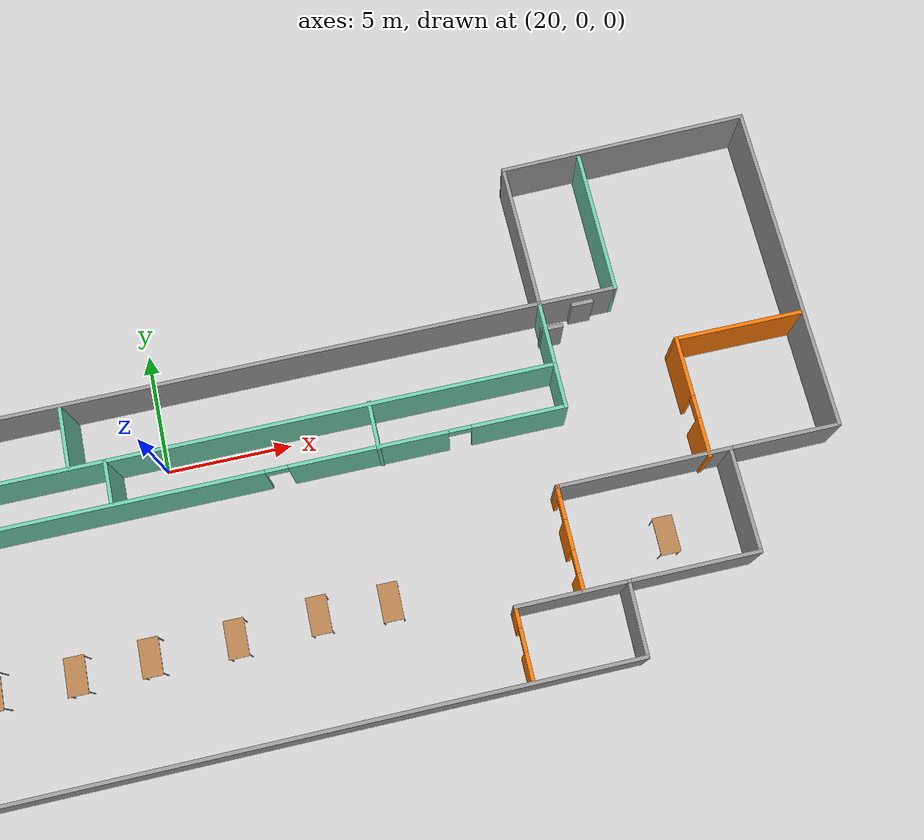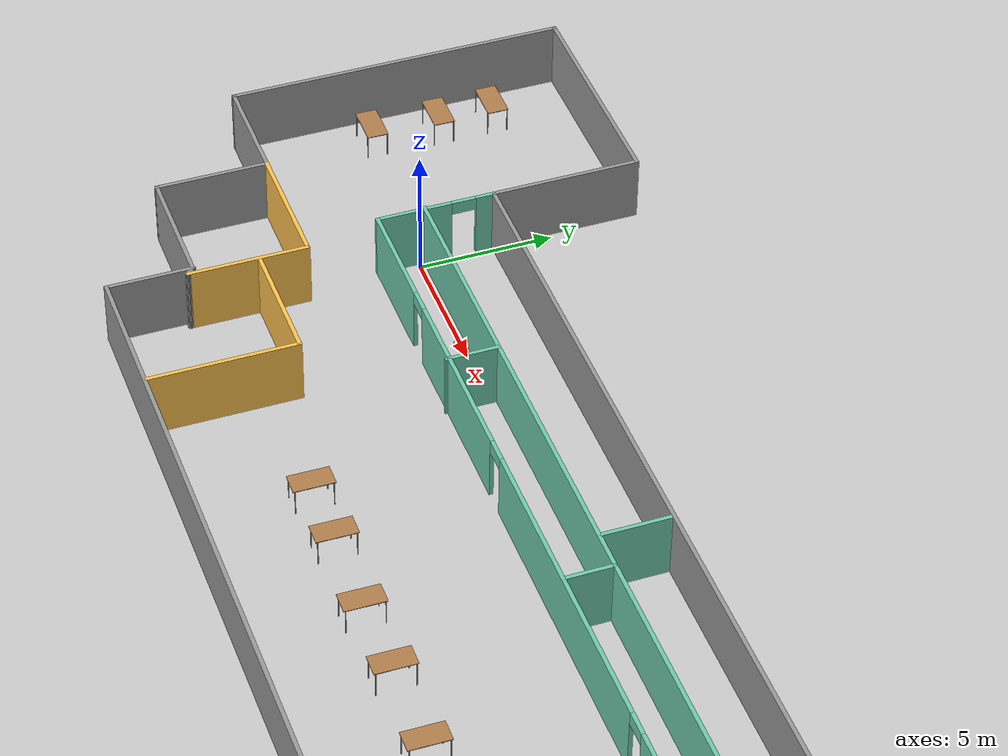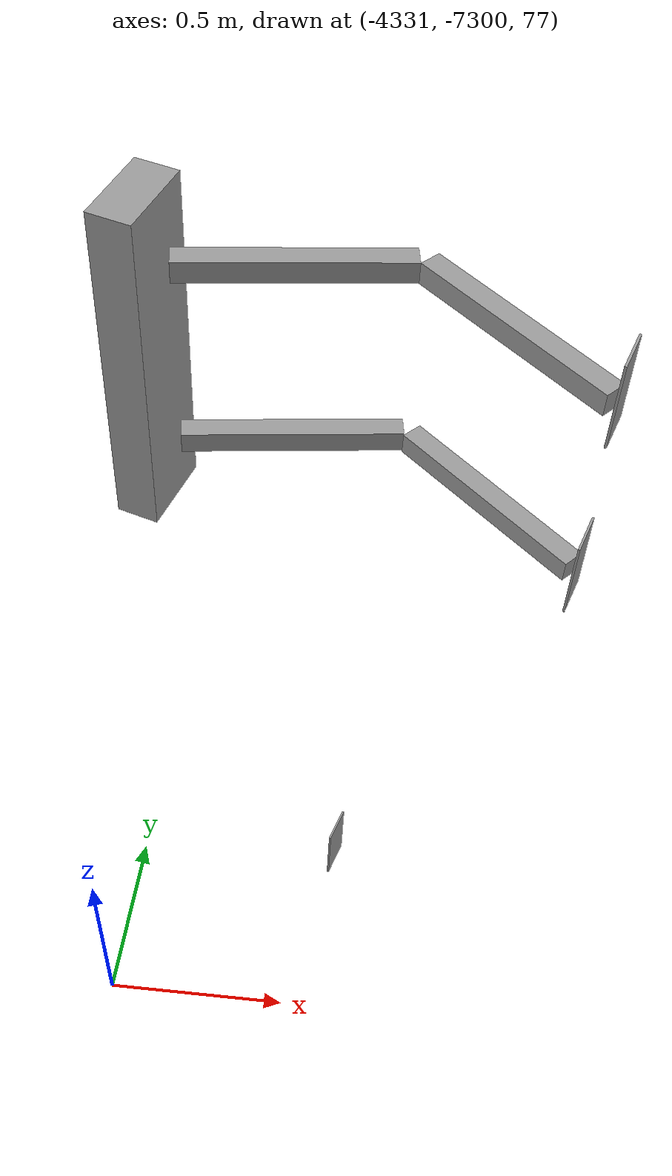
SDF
<sdf version="1.7">
 <world name="default">
  <plugin name="hello" filename="libhello.so"/>
  <light name="sun" type="directional">
   <pose>0 0 10 0 -0 0</pose>
   <diffuse>0.8 0.8 0.8 1</diffuse>
   <specular>0.2 0.2 0.2 1</specular>
   <attenuation>
    <range>1000</range>
    <constant>0.9</constant>
    <linear>0.01</linear>
    <quadratic>0.001</quadratic>
   </attenuation>
   <direction>-0.5 0.1 -0.9</direction>
   <spot><inner_angle>0</inner_angle><outer_angle>0</outer_angle><falloff>0</falloff></spot>
  </light>
  <model name="ground_plane">
   <static>1</static>
   <link name="link">
    <collision name="collision">
     <geometry><plane><normal>0 0 1</normal><size>100 100</size></plane></geometry>
     <surface>
      <contact><collide_bitmask>65535</collide_bitmask></contact>
      <friction><ode><mu>100</mu><mu2>50</mu2></ode></friction>
     </surface>
    </collision>
    <visual name="visual">
     <cast_shadows>0</cast_shadows>
     <geometry><plane><normal>0 0 1</normal><size>100 100</size></plane></geometry>
     <material>
      <script><uri>file://media/materials/scripts/gazebo.material</uri><name>Gazebo/Grey</name></script>
     </material>
    </visual>
   </link>
  </model>
  <gravity>0 0 -9.8</gravity>
  <magnetic_field>6e-06 2.3e-05 -4.2e-05</magnetic_field>
  <atmosphere type="adiabatic"/>
  <physics type="ode">
   <max_step_size>0.001</max_step_size>
   <real_time_factor>1</real_time_factor>
   <real_time_update_rate>1000</real_time_update_rate>
  </physics>
  <scene><ambient>0.4 0.4 0.4 1</ambient><background>0.7 0.7 0.7 1</background><shadows>1</shadows></scene>
  <spherical_coordinates>
   <surface_model>EARTH_WGS84</surface_model>
   <latitude_deg>0</latitude_deg>
   <longitude_deg>0</longitude_deg>
   <elevation>0</elevation>
   <heading_deg>0</heading_deg>
  </spherical_coordinates>
  <model name="Building">
   <pose>18.6806 -1.21003 0 0 -0 0</pose>
   <link name="Door_6">
    <collision name="Door_6_Collision">
     <geometry><box><size>0.9 0.17 2</size></box></geometry>
     <pose>0 0 1 0 -0 0</pose>
    </collision>
    <visual name="Door_6_Visual">
     <pose>0 0 1 0 -0 0</pose>
     <geometry><box><size>0.9 0.17 2</size></box></geometry>
     <material>
      <script><uri>file://media/materials/scripts/gazebo.material</uri><name>Gazebo/Grey</name></script>
     </material>
    </visual>
    <pose>17.5014 3.14748 0 0 -0 0</pose>
   </link>
   <link name="Door_8">
    <collision name="Door_8_Collision">
     <geometry><box><size>0.9 0.17 2</size></box></geometry>
     <pose>0 0 1 0 -0 0</pose>
    </collision>
    <visual name="Door_8_Visual">
     <pose>0 0 1 0 -0 0</pose>
     <geometry><box><size>0.9 0.17 2</size></box></geometry>
     <material>
      <script><uri>file://media/materials/scripts/gazebo.material</uri><name>Gazebo/Grey</name></script>
     </material>
    </visual>
    <pose>18.9298 3.8962 0 0 -0 0</pose>
   </link>
   <link name="Wall_1">
    <collision name="Wall_1_Collision">
     <geometry><box><size>12.75 0.15 2.5</size></box></geometry>
     <pose>0 0 1.25 0 -0 0</pose>
    </collision>
    <visual name="Wall_1_Visual">
     <pose>0 0 1.25 0 -0 0</pose>
     <geometry><box><size>12.75 0.15 2.5</size></box></geometry>
     <material>
      <script><uri>file://media/materials/scripts/gazebo.material</uri><name>Gazebo/Grey</name></script>
      <ambient>1 1 1 1</ambient>
     </material>
     <meta><layer>0</layer></meta>
    </visual>
    <pose>-27.2758 3.22483 0 0 -0 -1.5708</pose>
   </link>
   <link name="Wall_10">
    <collision name="Wall_10_Collision">
     <geometry><box><size>5.61451 0.15 2.5</size></box></geometry>
     <pose>0 0 1.25 0 -0 0</pose>
    </collision>
    <visual name="Wall_10_Visual">
     <pose>0 0 1.25 0 -0 0</pose>
     <geometry><box><size>5.61451 0.15 2.5</size></box></geometry>
     <material>
      <script><uri>file://media/materials/scripts/gazebo.material</uri><name>Gazebo/Grey</name></script>
      <ambient>1 1 1 1</ambient>
     </material>
     <meta><layer>0</layer></meta>
    </visual>
    <pose>-18.9258 6.79266 0 0 -0 -1.5708</pose>
   </link>
   <link name="Wall_11">
    <collision name="Wall_11_Collision">
     <geometry><box><size>36.25 0.15 2.5</size></box></geometry>
     <pose>0 0 1.25 0 -0 0</pose>
    </collision>
    <visual name="Wall_11_Visual">
     <pose>0 0 1.25 0 -0 0</pose>
     <geometry><box><size>36.25 0.15 2.5</size></box></geometry>
     <material>
      <script><uri>file://media/materials/scripts/gazebo.material</uri><name>Gazebo/Grey</name></script>
      <ambient>1 1 1 1</ambient>
     </material>
     <meta><layer>0</layer></meta>
    </visual>
    <pose>-0.875826 4.0605 0 0 -0 0</pose>
   </link>
   <link name="Wall_12">
    <collision name="Wall_12_Collision">
     <geometry><box><size>6.13837 0.15 2.5</size></box></geometry>
     <pose>0 0 1.25 0 -0 0</pose>
    </collision>
    <visual name="Wall_12_Visual">
     <pose>0 0 1.25 0 -0 0</pose>
     <geometry><box><size>6.13837 0.15 2.5</size></box></geometry>
     <material>
      <script><uri>file://media/materials/scripts/gazebo.material</uri><name>Gazebo/Grey</name></script>
      <ambient>1 1 1 1</ambient>
     </material>
     <meta><layer>0</layer></meta>
    </visual>
    <pose>17.1516 7.0546 0 0 -0 1.57835</pose>
   </link>
   <link name="Wall_13">
    <collision name="Wall_13_Collision">
     <geometry><box><size>10.2977 0.15 2.5</size></box></geometry>
     <pose>0 0 1.25 0 -0 0</pose>
    </collision>
    <visual name="Wall_13_Visual">
     <pose>0 0 1.25 0 -0 0</pose>
     <geometry><box><size>10.2977 0.15 2.5</size></box></geometry>
     <material>
      <script><uri>file://media/materials/scripts/gazebo.material</uri><name>Gazebo/Grey</name></script>
      <ambient>1 1 1 1</ambient>
     </material>
     <meta><layer>0</layer></meta>
    </visual>
    <pose>22.2016 10.1618 0 0 -0 0.022285</pose>
   </link>
   <link name="Wall_14">
    <collision name="Wall_14_Collision">
     <geometry><box><size>13.75 0.15 2.5</size></box></geometry>
     <pose>0 0 1.25 0 -0 0</pose>
    </collision>
    <visual name="Wall_14_Visual">
     <pose>0 0 1.25 0 -0 0</pose>
     <geometry><box><size>13.75 0.15 2.5</size></box></geometry>
     <material>
      <script><uri>file://media/materials/scripts/gazebo.material</uri><name>Gazebo/Grey</name></script>
      <ambient>1 1 1 1</ambient>
     </material>
     <meta><layer>0</layer></meta>
    </visual>
    <pose>27.2742 3.47483 0 0 -0 -1.5708</pose>
   </link>
   <link name="Wall_15">
    <collision name="Wall_15_Collision">
     <geometry><box><size>4.5 0.15 2.5</size></box></geometry>
     <pose>0 0 1.25 0 -0 0</pose>
    </collision>
    <visual name="Wall_15_Visual">
     <pose>0 0 1.25 0 -0 0</pose>
     <geometry><box><size>4.5 0.15 2.5</size></box></geometry>
     <material>
      <script><uri>file://media/materials/scripts/gazebo.material</uri><name>Gazebo/Grey</name></script>
      <ambient>1 1 1 1</ambient>
     </material>
     <meta><layer>0</layer></meta>
    </visual>
    <pose>25.0992 -3.32517 0 0 -0 3.14159</pose>
   </link>
   <link name="Wall_16">
    <collision name="Wall_16_Collision">
     <geometry><box><size>4.25 0.15 2.5</size></box></geometry>
     <pose>0 0 1.25 0 -0 0</pose>
    </collision>
    <visual name="Wall_16_Visual">
     <pose>0 0 1.25 0 -0 0</pose>
     <geometry><box><size>4.25 0.15 2.5</size></box></geometry>
     <material>
      <script><uri>file://media/materials/scripts/gazebo.material</uri><name>Gazebo/Grey</name></script>
      <ambient>1 1 1 1</ambient>
     </material>
     <meta><layer>0</layer></meta>
    </visual>
    <pose>22.9242 -5.37517 0 0 -0 -1.5708</pose>
   </link>
   <link name="Wall_2">
    <collision name="Wall_2_Collision">
     <geometry><box><size>4.25 0.15 2.5</size></box></geometry>
     <pose>0 0 1.25 0 -0 0</pose>
    </collision>
    <visual name="Wall_2_Visual">
     <pose>0 0 1.25 0 -0 0</pose>
     <geometry><box><size>4.25 0.15 2.5</size></box></geometry>
     <material>
      <script><uri>file://media/materials/scripts/gazebo.material</uri><name>Gazebo/Grey</name></script>
      <ambient>1 1 1 1</ambient>
     </material>
     <meta><layer>0</layer></meta>
    </visual>
    <pose>-25.2258 -3.07517 0 0 -0 0</pose>
   </link>
   <link name="Wall_20">
    <collision name="Wall_20_Collision">
     <geometry><box><size>5.2502 0.15 2.5</size></box></geometry>
     <pose>0 0 1.25 0 -0 0</pose>
    </collision>
    <visual name="Wall_20_Visual">
     <pose>0 0 1.25 0 -0 0</pose>
     <geometry><box><size>5.2502 0.15 2.5</size></box></geometry>
     <material>
      <script><uri>file://media/materials/scripts/gazebo.material</uri><name>Gazebo/Grey</name></script>
      <ambient>1 1 1 1</ambient>
     </material>
     <meta><layer>0</layer></meta>
    </visual>
    <pose>20.3742 -7.42517 0 0 -0 3.14159</pose>
   </link>
   <link name="Wall_21">
    <collision name="Wall_21_Collision">
     <geometry><box><size>3.00044 0.15 2.5</size></box></geometry>
     <pose>0 0 1.25 0 -0 0</pose>
    </collision>
    <visual name="Wall_21_Visual">
     <pose>0 0 1.25 0 -0 0</pose>
     <geometry><box><size>3.00044 0.15 2.5</size></box></geometry>
     <material>
      <script><uri>file://media/materials/scripts/gazebo.material</uri><name>Gazebo/Grey</name></script>
      <ambient>1 1 1 1</ambient>
     </material>
     <meta><layer>0</layer></meta>
    </visual>
    <pose>17.7992 -8.85017 0 0 -0 -1.58834</pose>
   </link>
   <link name="Wall_3">
    <collision name="Wall_3_Collision">
     <geometry><box><size>4.25 0.15 2.5</size></box></geometry>
     <pose>0 0 1.25 0 -0 0</pose>
    </collision>
    <visual name="Wall_3_Visual">
     <pose>0 0 1.25 0 -0 0</pose>
     <geometry><box><size>4.25 0.15 2.5</size></box></geometry>
     <material>
      <script><uri>file://media/materials/scripts/gazebo.material</uri><name>Gazebo/Grey</name></script>
      <ambient>1 1 1 1</ambient>
     </material>
     <meta><layer>0</layer></meta>
    </visual>
    <pose>-23.1758 -5.12517 0 0 -0 -1.5708</pose>
   </link>
   <link name="Wall_32">
    <collision name="Wall_32_Collision">
     <geometry><box><size>4.5 0.15 2.5</size></box></geometry>
     <pose>0 0 1.25 0 -0 0</pose>
    </collision>
    <visual name="Wall_32_Visual">
     <pose>0 0 1.25 0 -0 0</pose>
     <geometry><box><size>4.5 0.15 2.5</size></box></geometry>
     <material>
      <script><uri>file://media/materials/scripts/gazebo.material</uri><name>Gazebo/Grey</name></script>
      <ambient>0.435294 0.796078 0.67451 1</ambient>
     </material>
     <meta><layer>0</layer></meta>
    </visual>
    <pose>17.1742 1.8855 0 0 -0 -1.5708</pose>
   </link>
   <link name="Wall_33">
    <pose>-0.875826 -0.289499 0 0 -0 3.14159</pose>
    <visual name="Wall_33_Visual_0">
     <pose>-16.2149 0 1.25 0 -0 0</pose>
     <geometry><box><size>3.82029 0.15 2.5</size></box></geometry>
     <material>
      <script><uri>file://media/materials/scripts/gazebo.material</uri><name>Gazebo/Grey</name></script>
      <ambient>0.435294 0.796078 0.67451 1</ambient>
     </material>
     <meta><layer>0</layer></meta>
    </visual>
    <collision name="Wall_33_Collision_0">
     <geometry><box><size>3.82029 0.15 2.5</size></box></geometry>
     <pose>-16.2149 0 1.25 0 -0 0</pose>
    </collision>
    <visual name="Wall_33_Visual_1">
     <pose>-10.2593 0 1.25 0 -0 0</pose>
     <geometry><box><size>6.2908 0.15 2.5</size></box></geometry>
     <material>
      <script><uri>file://media/materials/scripts/gazebo.material</uri><name>Gazebo/Grey</name></script>
      <ambient>0.435294 0.796078 0.67451 1</ambient>
     </material>
     <meta><layer>0</layer></meta>
    </visual>
    <collision name="Wall_33_Collision_1">
     <geometry><box><size>6.2908 0.15 2.5</size></box></geometry>
     <pose>-10.2593 0 1.25 0 -0 0</pose>
    </collision>
    <visual name="Wall_33_Visual_2">
     <pose>-0.445449 0 1.25 0 -0 0</pose>
     <geometry><box><size>11.5369 0.15 2.5</size></box></geometry>
     <material>
      <script><uri>file://media/materials/scripts/gazebo.material</uri><name>Gazebo/Grey</name></script>
      <ambient>0.435294 0.796078 0.67451 1</ambient>
     </material>
     <meta><layer>0</layer></meta>
    </visual>
    <collision name="Wall_33_Collision_2">
     <geometry><box><size>11.5369 0.15 2.5</size></box></geometry>
     <pose>-0.445449 0 1.25 0 -0 0</pose>
    </collision>
    <visual name="Wall_33_Visual_3">
     <pose>9.63976 0 1.25 0 -0 0</pose>
     <geometry><box><size>6.8335 0.15 2.5</size></box></geometry>
     <material>
      <script><uri>file://media/materials/scripts/gazebo.material</uri><name>Gazebo/Grey</name></script>
      <ambient>0.435294 0.796078 0.67451 1</ambient>
     </material>
     <meta><layer>0</layer></meta>
    </visual>
    <collision name="Wall_33_Collision_3">
     <geometry><box><size>6.8335 0.15 2.5</size></box></geometry>
     <pose>9.63976 0 1.25 0 -0 0</pose>
    </collision>
    <visual name="Wall_33_Visual_4">
     <pose>16.0408 0 1.25 0 -0 0</pose>
     <geometry><box><size>4.16848 0.15 2.5</size></box></geometry>
     <material>
      <script><uri>file://media/materials/scripts/gazebo.material</uri><name>Gazebo/Grey</name></script>
      <ambient>0.435294 0.796078 0.67451 1</ambient>
     </material>
     <meta><layer>0</layer></meta>
    </visual>
    <collision name="Wall_33_Collision_4">
     <geometry><box><size>4.16848 0.15 2.5</size></box></geometry>
     <pose>16.0408 0 1.25 0 -0 0</pose>
    </collision>
    <visual name="Wall_33_Visual_5">
     <pose>-13.8547 0 2.25 0 -0 0</pose>
     <geometry><box><size>0.9 0.15 0.5</size></box></geometry>
     <material>
      <script><uri>file://media/materials/scripts/gazebo.material</uri><name>Gazebo/Grey</name></script>
      <ambient>0.435294 0.796078 0.67451 1</ambient>
     </material>
     <meta><layer>0</layer></meta>
    </visual>
    <collision name="Wall_33_Collision_5">
     <geometry><box><size>0.9 0.15 0.5</size></box></geometry>
     <pose>-13.8547 0 2.25 0 -0 0</pose>
    </collision>
    <visual name="Wall_33_Visual_6">
     <pose>-6.66391 0 2.25 0 -0 0</pose>
     <geometry><box><size>0.9 0.15 0.5</size></box></geometry>
     <material>
      <script><uri>file://media/materials/scripts/gazebo.material</uri><name>Gazebo/Grey</name></script>
      <ambient>0.435294 0.796078 0.67451 1</ambient>
     </material>
     <meta><layer>0</layer></meta>
    </visual>
    <collision name="Wall_33_Collision_6">
     <geometry><box><size>0.9 0.15 0.5</size></box></geometry>
     <pose>-6.66391 0 2.25 0 -0 0</pose>
    </collision>
    <visual name="Wall_33_Visual_7">
     <pose>5.77301 0 2.25 0 -0 0</pose>
     <geometry><box><size>0.9 0.15 0.5</size></box></geometry>
     <material>
      <script><uri>file://media/materials/scripts/gazebo.material</uri><name>Gazebo/Grey</name></script>
      <ambient>0.435294 0.796078 0.67451 1</ambient>
     </material>
     <meta><layer>0</layer></meta>
    </visual>
    <collision name="Wall_33_Collision_7">
     <geometry><box><size>0.9 0.15 0.5</size></box></geometry>
     <pose>5.77301 0 2.25 0 -0 0</pose>
    </collision>
    <visual name="Wall_33_Visual_8">
     <pose>13.5065 0 2.25 0 -0 0</pose>
     <geometry><box><size>0.9 0.15 0.5</size></box></geometry>
     <material>
      <script><uri>file://media/materials/scripts/gazebo.material</uri><name>Gazebo/Grey</name></script>
      <ambient>0.435294 0.796078 0.67451 1</ambient>
     </material>
     <meta><layer>0</layer></meta>
    </visual>
    <collision name="Wall_33_Collision_8">
     <geometry><box><size>0.9 0.15 0.5</size></box></geometry>
     <pose>13.5065 0 2.25 0 -0 0</pose>
    </collision>
   </link>
   <link name="Wall_35">
    <pose>-18.9258 1.8855 0 0 -0 -1.5708</pose>
    <visual name="Wall_35_Visual_0">
     <pose>-1.86792 0 1.25 0 -0 0</pose>
     <geometry><box><size>0.764151 0.15 2.5</size></box></geometry>
     <material>
      <script><uri>file://media/materials/scripts/gazebo.material</uri><name>Gazebo/Grey</name></script>
      <ambient>0.435294 0.796078 0.67451 1</ambient>
     </material>
     <meta><layer>0</layer></meta>
    </visual>
    <collision name="Wall_35_Collision_0">
     <geometry><box><size>0.764151 0.15 2.5</size></box></geometry>
     <pose>-1.86792 0 1.25 0 -0 0</pose>
    </collision>
    <visual name="Wall_35_Visual_1">
     <pose>0.832076 0 1.25 0 -0 0</pose>
     <geometry><box><size>2.83585 0.15 2.5</size></box></geometry>
     <material>
      <script><uri>file://media/materials/scripts/gazebo.material</uri><name>Gazebo/Grey</name></script>
      <ambient>0.435294 0.796078 0.67451 1</ambient>
     </material>
     <meta><layer>0</layer></meta>
    </visual>
    <collision name="Wall_35_Collision_1">
     <geometry><box><size>2.83585 0.15 2.5</size></box></geometry>
     <pose>0.832076 0 1.25 0 -0 0</pose>
    </collision>
    <visual name="Wall_35_Visual_2">
     <pose>-1.03585 0 2.25 0 -0 0</pose>
     <geometry><box><size>0.9 0.15 0.5</size></box></geometry>
     <material>
      <script><uri>file://media/materials/scripts/gazebo.material</uri><name>Gazebo/Grey</name></script>
      <ambient>0.435294 0.796078 0.67451 1</ambient>
     </material>
     <meta><layer>0</layer></meta>
    </visual>
    <collision name="Wall_35_Collision_2">
     <geometry><box><size>0.9 0.15 0.5</size></box></geometry>
     <pose>-1.03585 0 2.25 0 -0 0</pose>
    </collision>
   </link>
   <link name="Wall_38">
    <collision name="Wall_38_Collision">
     <geometry><box><size>36.25 0.15 2.5</size></box></geometry>
     <pose>0 0 1.25 0 -0 0</pose>
    </collision>
    <visual name="Wall_38_Visual">
     <pose>0 0 1.25 0 -0 0</pose>
     <geometry><box><size>36.25 0.15 2.5</size></box></geometry>
     <material>
      <script><uri>file://media/materials/scripts/gazebo.material</uri><name>Gazebo/Grey</name></script>
      <ambient>0.435294 0.796078 0.67451 1</ambient>
     </material>
     <meta><layer>0</layer></meta>
    </visual>
    <pose>-0.945311 1.47414 0 0 -0 0</pose>
   </link>
   <link name="Wall_4">
    <collision name="Wall_4_Collision">
     <geometry><box><size>4.75 0.15 2.5</size></box></geometry>
     <pose>0 0 1.25 0 -0 0</pose>
    </collision>
    <visual name="Wall_4_Visual">
     <pose>0 0 1.25 0 -0 0</pose>
     <geometry><box><size>4.75 0.15 2.5</size></box></geometry>
     <material>
      <script><uri>file://media/materials/scripts/gazebo.material</uri><name>Gazebo/Grey</name></script>
      <ambient>1 1 1 1</ambient>
     </material>
     <meta><layer>0</layer></meta>
    </visual>
    <pose>-20.8758 -7.17517 0 0 -0 0</pose>
   </link>
   <link name="Wall_42">
    <collision name="Wall_42_Collision">
     <geometry><box><size>2 0.15 2.5</size></box></geometry>
     <pose>0 0 1.25 0 -0 0</pose>
    </collision>
    <visual name="Wall_42_Visual">
     <pose>0 0 1.25 0 -0 0</pose>
     <geometry><box><size>2 0.15 2.5</size></box></geometry>
     <material>
      <script><uri>file://media/materials/scripts/gazebo.material</uri><name>Gazebo/Grey</name></script>
      <ambient>0.435294 0.796078 0.67451 1</ambient>
     </material>
     <meta><layer>0</layer></meta>
    </visual>
    <pose>-11.307 0.549144 0 0 -0 -1.5708</pose>
   </link>
   <link name="Wall_44">
    <collision name="Wall_44_Collision">
     <geometry><box><size>1.75 0.15 2.5</size></box></geometry>
     <pose>0 0 1.25 0 -0 0</pose>
    </collision>
    <visual name="Wall_44_Visual">
     <pose>0 0 1.25 0 -0 0</pose>
     <geometry><box><size>1.75 0.15 2.5</size></box></geometry>
     <material>
      <script><uri>file://media/materials/scripts/gazebo.material</uri><name>Gazebo/Grey</name></script>
      <ambient>0.435294 0.796078 0.67451 1</ambient>
     </material>
     <meta><layer>0</layer></meta>
    </visual>
    <pose>-0.54344 0.628919 0 0 -0 -1.5708</pose>
   </link>
   <link name="Wall_46">
    <collision name="Wall_46_Collision">
     <geometry><box><size>2 0.15 2.5</size></box></geometry>
     <pose>0 0 1.25 0 -0 0</pose>
    </collision>
    <visual name="Wall_46_Visual">
     <pose>0 0 1.25 0 -0 0</pose>
     <geometry><box><size>2 0.15 2.5</size></box></geometry>
     <material>
      <script><uri>file://media/materials/scripts/gazebo.material</uri><name>Gazebo/Grey</name></script>
      <ambient>0.435294 0.796078 0.67451 1</ambient>
     </material>
     <meta><layer>0</layer></meta>
    </visual>
    <pose>9.7679 0.59437 0 0 -0 -1.5708</pose>
   </link>
   <link name="Wall_5">
    <collision name="Wall_5_Collision">
     <geometry><box><size>3.25 0.15 2.5</size></box></geometry>
     <pose>0 0 1.25 0 -0 0</pose>
    </collision>
    <visual name="Wall_5_Visual">
     <pose>0 0 1.25 0 -0 0</pose>
     <geometry><box><size>3.25 0.15 2.5</size></box></geometry>
     <material>
      <script><uri>file://media/materials/scripts/gazebo.material</uri><name>Gazebo/Grey</name></script>
      <ambient>1 1 1 1</ambient>
     </material>
     <meta><layer>0</layer></meta>
    </visual>
    <pose>-18.5758 -8.72517 0 0 -0 -1.5708</pose>
   </link>
   <link name="Wall_51">
    <collision name="Wall_51_Collision">
     <geometry><box><size>2.5 0.15 2.5</size></box></geometry>
     <pose>0 0 1.25 0 -0 0</pose>
    </collision>
    <visual name="Wall_51_Visual">
     <pose>0 0 1.25 0 -0 0</pose>
     <geometry><box><size>2.5 0.15 2.5</size></box></geometry>
     <material>
      <script><uri>file://media/materials/scripts/gazebo.material</uri><name>Gazebo/Grey</name></script>
      <ambient>0.435294 0.796078 0.67451 1</ambient>
     </material>
     <meta><layer>0</layer></meta>
    </visual>
    <pose>-1.94542 2.7396 0 0 -0 1.5708</pose>
   </link>
   <link name="Wall_55">
    <collision name="Wall_55_Collision">
     <geometry><box><size>3.25 0.15 2.5</size></box></geometry>
     <pose>0 0 1.25 0 -0 0</pose>
    </collision>
    <visual name="Wall_55_Visual">
     <pose>0 0 1.25 0 -0 0</pose>
     <geometry><box><size>3.25 0.15 2.5</size></box></geometry>
     <material>
      <script><uri>file://media/materials/scripts/gazebo.material</uri><name>Gazebo/Grey</name></script>
      <ambient>1 1 1 1</ambient>
     </material>
     <meta><layer>0</layer></meta>
    </visual>
    <pose>18.7242 4.0605 0 0 -0 0</pose>
   </link>
   <link name="Wall_56">
    <collision name="Wall_56_Collision">
     <geometry><box><size>6 0.15 2.5</size></box></geometry>
     <pose>0 0 1.25 0 -0 0</pose>
    </collision>
    <visual name="Wall_56_Visual">
     <pose>0 0 1.25 0 -0 0</pose>
     <geometry><box><size>6 0.15 2.5</size></box></geometry>
     <material>
      <script><uri>file://media/materials/scripts/gazebo.material</uri><name>Gazebo/Grey</name></script>
      <ambient>0.435294 0.796078 0.67451 1</ambient>
     </material>
     <meta><layer>0</layer></meta>
    </visual>
    <pose>20.2742 6.9855 0 0 -0 1.5708</pose>
   </link>
   <link name="Wall_59">
    <collision name="Wall_59_Collision">
     <geometry><box><size>5 0.15 2.5</size></box></geometry>
     <pose>0 0 1.25 0 -0 0</pose>
    </collision>
    <visual name="Wall_59_Visual">
     <pose>0 0 1.25 0 -0 0</pose>
     <geometry><box><size>5 0.15 2.5</size></box></geometry>
     <material>
      <script><uri>file://media/materials/scripts/gazebo.material</uri><name>Gazebo/Grey</name></script>
      <ambient>1 0.764706 0.305882 1</ambient>
     </material>
     <meta><layer>0</layer></meta>
    </visual>
    <pose>-20.7508 -3.07517 0 0 -0 0</pose>
   </link>
   <link name="Wall_6">
    <collision name="Wall_6_Collision">
     <geometry><box><size>36.5 0.15 2.5</size></box></geometry>
     <pose>0 0 1.25 0 -0 0</pose>
    </collision>
    <visual name="Wall_6_Visual">
     <pose>0 0 1.25 0 -0 0</pose>
     <geometry><box><size>36.5 0.15 2.5</size></box></geometry>
     <material>
      <script><uri>file://media/materials/scripts/gazebo.material</uri><name>Gazebo/Grey</name></script>
      <ambient>1 1 1 1</ambient>
     </material>
     <meta><layer>0</layer></meta>
    </visual>
    <pose>-0.400826 -10.2752 0 0 -0 0</pose>
   </link>
   <link name="Wall_60">
    <collision name="Wall_60_Collision">
     <geometry><box><size>4.5 0.15 2.5</size></box></geometry>
     <pose>0 0 1.25 0 -0 0</pose>
    </collision>
    <visual name="Wall_60_Visual">
     <pose>0 0 1.25 0 -0 0</pose>
     <geometry><box><size>4.5 0.15 2.5</size></box></geometry>
     <material>
      <script><uri>file://media/materials/scripts/gazebo.material</uri><name>Gazebo/Grey</name></script>
      <ambient>1 0.764706 0.305882 1</ambient>
     </material>
     <meta><layer>0</layer></meta>
    </visual>
    <pose>-18.3258 -5.25017 0 0 -0 -1.5708</pose>
   </link>
   <link name="Wall_62">
    <collision name="Wall_62_Collision">
     <geometry><box><size>4.75 0.15 2.5</size></box></geometry>
     <pose>0 0 1.25 0 -0 0</pose>
    </collision>
    <visual name="Wall_62_Visual">
     <pose>0 0 1.25 0 -0 0</pose>
     <geometry><box><size>4.75 0.15 2.5</size></box></geometry>
     <material>
      <script><uri>file://media/materials/scripts/gazebo.material</uri><name>Gazebo/Grey</name></script>
      <ambient>1 0.764706 0.305882 1</ambient>
     </material>
     <meta><layer>0</layer></meta>
    </visual>
    <pose>-15.9722 -4.8361 0 0 -0 0</pose>
   </link>
   <link name="Wall_63">
    <collision name="Wall_63_Collision">
     <geometry><box><size>5.5 0.15 2.5</size></box></geometry>
     <pose>0 0 1.25 0 -0 0</pose>
    </collision>
    <visual name="Wall_63_Visual">
     <pose>0 0 1.25 0 -0 0</pose>
     <geometry><box><size>5.5 0.15 2.5</size></box></geometry>
     <material>
      <script><uri>file://media/materials/scripts/gazebo.material</uri><name>Gazebo/Grey</name></script>
      <ambient>1 0.764706 0.305882 1</ambient>
     </material>
     <meta><layer>0</layer></meta>
    </visual>
    <pose>-13.6722 -7.5111 0 0 -0 -1.5708</pose>
   </link>
   <link name="Wall_65">
    <collision name="Wall_65_Collision">
     <geometry><box><size>0.15 0.15 2.5</size></box></geometry>
     <pose>0 0 1.25 0 -0 0</pose>
    </collision>
    <visual name="Wall_65_Visual">
     <pose>0 0 1.25 0 -0 0</pose>
     <geometry><box><size>0.15 0.15 2.5</size></box></geometry>
     <material>
      <script><uri>file://media/materials/scripts/gazebo.material</uri><name>Gazebo/Grey</name></script>
      <ambient>1 1 1 1</ambient>
     </material>
     <meta><layer>0</layer></meta>
    </visual>
    <pose>-18.3258 -7.42517 0 0 -0 0</pose>
   </link>
   <link name="Wall_67">
    <collision name="Wall_67_Collision">
     <geometry><box><size>0.503553 0.15 2.5</size></box></geometry>
     <pose>0 0 1.25 0 -0 0</pose>
    </collision>
    <visual name="Wall_67_Visual">
     <pose>0 0 1.25 0 -0 0</pose>
     <geometry><box><size>0.503553 0.15 2.5</size></box></geometry>
     <material>
      <script><uri>file://media/materials/scripts/gazebo.material</uri><name>Gazebo/Grey</name></script>
      <ambient>1 1 1 1</ambient>
     </material>
     <meta><layer>0</layer></meta>
    </visual>
    <pose>-18.4508 -7.30017 0 0 -0 2.35619</pose>
   </link>
   <link name="Wall_69">
    <collision name="Wall_69_Collision">
     <geometry><box><size>5.25 0.15 2.5</size></box></geometry>
     <pose>0 0 1.25 0 -0 0</pose>
    </collision>
    <visual name="Wall_69_Visual">
     <pose>0 0 1.25 0 -0 0</pose>
     <geometry><box><size>5.25 0.15 2.5</size></box></geometry>
     <material>
      <script><uri>file://media/materials/scripts/gazebo.material</uri><name>Gazebo/Grey</name></script>
      <ambient>0.996078 0.47451 0.0196078 1</ambient>
     </material>
     <meta><layer>0</layer></meta>
    </visual>
    <pose>24.63 1.42961 0 0 -0 3.14159</pose>
   </link>
   <link name="Wall_70">
    <pose>22.08 -0.995387 0 0 -0 -1.5708</pose>
    <visual name="Wall_70_Visual_0">
     <pose>-1.25768 0 1.25 0 -0 0</pose>
     <geometry><box><size>2.48464 0.15 2.5</size></box></geometry>
     <material>
      <script><uri>file://media/materials/scripts/gazebo.material</uri><name>Gazebo/Grey</name></script>
      <ambient>0.996078 0.47451 0.0196078 1</ambient>
     </material>
     <meta><layer>0</layer></meta>
    </visual>
    <collision name="Wall_70_Collision_0">
     <geometry><box><size>2.48464 0.15 2.5</size></box></geometry>
     <pose>-1.25768 0 1.25 0 -0 0</pose>
    </collision>
    <visual name="Wall_70_Visual_1">
     <pose>1.69232 0 1.25 0 -0 0</pose>
     <geometry><box><size>1.61536 0.15 2.5</size></box></geometry>
     <material>
      <script><uri>file://media/materials/scripts/gazebo.material</uri><name>Gazebo/Grey</name></script>
      <ambient>0.996078 0.47451 0.0196078 1</ambient>
     </material>
     <meta><layer>0</layer></meta>
    </visual>
    <collision name="Wall_70_Collision_1">
     <geometry><box><size>1.61536 0.15 2.5</size></box></geometry>
     <pose>1.69232 0 1.25 0 -0 0</pose>
    </collision>
    <visual name="Wall_70_Visual_2">
     <pose>0.434642 0 2.25 0 -0 0</pose>
     <geometry><box><size>0.9 0.15 0.5</size></box></geometry>
     <material>
      <script><uri>file://media/materials/scripts/gazebo.material</uri><name>Gazebo/Grey</name></script>
      <ambient>0.996078 0.47451 0.0196078 1</ambient>
     </material>
     <meta><layer>0</layer></meta>
    </visual>
    <collision name="Wall_70_Collision_2">
     <geometry><box><size>0.9 0.15 0.5</size></box></geometry>
     <pose>0.434642 0 2.25 0 -0 0</pose>
    </collision>
   </link>
   <link name="Wall_72">
    <collision name="Wall_72_Collision">
     <geometry><box><size>7 0.15 2.5</size></box></geometry>
     <pose>0 0 1.25 0 -0 0</pose>
    </collision>
    <visual name="Wall_72_Visual">
     <pose>0 0 1.25 0 -0 0</pose>
     <geometry><box><size>7 0.15 2.5</size></box></geometry>
     <material>
      <script><uri>file://media/materials/scripts/gazebo.material</uri><name>Gazebo/Grey</name></script>
      <ambient>1 1 1 1</ambient>
     </material>
     <meta><layer>0</layer></meta>
    </visual>
    <pose>19.4992 -3.32517 0 0 -0 3.14159</pose>
   </link>
   <link name="Wall_74">
    <collision name="Wall_74_Collision">
     <geometry><box><size>4.5 0.15 2.5</size></box></geometry>
     <pose>0 0 1.25 0 -0 0</pose>
    </collision>
    <visual name="Wall_74_Visual">
     <pose>0 0 1.25 0 -0 0</pose>
     <geometry><box><size>4.5 0.15 2.5</size></box></geometry>
     <material>
      <script><uri>file://media/materials/scripts/gazebo.material</uri><name>Gazebo/Grey</name></script>
      <ambient>1 1 1 1</ambient>
     </material>
     <meta><layer>0</layer></meta>
    </visual>
    <pose>15.6492 -7.42517 0 0 -0 3.14159</pose>
   </link>
   <link name="Wall_75">
    <pose>13.4742 -8.85017 0 0 -0 -1.5708</pose>
    <visual name="Wall_75_Visual_0">
     <pose>-1.06655 0 1.25 0 -0 0</pose>
     <geometry><box><size>0.866898 0.15 2.5</size></box></geometry>
     <material>
      <script><uri>file://media/materials/scripts/gazebo.material</uri><name>Gazebo/Grey</name></script>
      <ambient>0.996078 0.47451 0.0196078 1</ambient>
     </material>
     <meta><layer>0</layer></meta>
    </visual>
    <collision name="Wall_75_Collision_0">
     <geometry><box><size>0.866898 0.15 2.5</size></box></geometry>
     <pose>-1.06655 0 1.25 0 -0 0</pose>
    </collision>
    <visual name="Wall_75_Visual_1">
     <pose>0.883449 0 1.25 0 -0 0</pose>
     <geometry><box><size>1.2331 0.15 2.5</size></box></geometry>
     <material>
      <script><uri>file://media/materials/scripts/gazebo.material</uri><name>Gazebo/Grey</name></script>
      <ambient>0.996078 0.47451 0.0196078 1</ambient>
     </material>
     <meta><layer>0</layer></meta>
    </visual>
    <collision name="Wall_75_Collision_1">
     <geometry><box><size>1.2331 0.15 2.5</size></box></geometry>
     <pose>0.883449 0 1.25 0 -0 0</pose>
    </collision>
    <visual name="Wall_75_Visual_2">
     <pose>-0.183102 0 2.25 0 -0 0</pose>
     <geometry><box><size>0.9 0.15 0.5</size></box></geometry>
     <material>
      <script><uri>file://media/materials/scripts/gazebo.material</uri><name>Gazebo/Grey</name></script>
      <ambient>0.996078 0.47451 0.0196078 1</ambient>
     </material>
     <meta><layer>0</layer></meta>
    </visual>
    <collision name="Wall_75_Collision_2">
     <geometry><box><size>0.9 0.15 0.5</size></box></geometry>
     <pose>-0.183102 0 2.25 0 -0 0</pose>
    </collision>
   </link>
   <link name="Wall_77">
    <pose>16.0742 -5.37517 0 0 -0 -1.5708</pose>
    <visual name="Wall_77_Visual_0">
     <pose>-1.88444 0 1.25 0 -0 0</pose>
     <geometry><box><size>0.481127 0.15 2.5</size></box></geometry>
     <material>
      <script><uri>file://media/materials/scripts/gazebo.material</uri><name>Gazebo/Grey</name></script>
      <ambient>0.996078 0.47451 0.0196078 1</ambient>
     </material>
     <meta><layer>0</layer></meta>
    </visual>
    <collision name="Wall_77_Collision_0">
     <geometry><box><size>0.481127 0.15 2.5</size></box></geometry>
     <pose>-1.88444 0 1.25 0 -0 0</pose>
    </collision>
    <visual name="Wall_77_Visual_1">
     <pose>-0.147193 0 1.25 0 -0 0</pose>
     <geometry><box><size>1.19336 0.15 2.5</size></box></geometry>
     <material>
      <script><uri>file://media/materials/scripts/gazebo.material</uri><name>Gazebo/Grey</name></script>
      <ambient>0.996078 0.47451 0.0196078 1</ambient>
     </material>
     <meta><layer>0</layer></meta>
    </visual>
    <collision name="Wall_77_Collision_1">
     <geometry><box><size>1.19336 0.15 2.5</size></box></geometry>
     <pose>-0.147193 0 1.25 0 -0 0</pose>
    </collision>
    <visual name="Wall_77_Visual_2">
     <pose>1.73724 0 1.25 0 -0 0</pose>
     <geometry><box><size>0.775513 0.15 2.5</size></box></geometry>
     <material>
      <script><uri>file://media/materials/scripts/gazebo.material</uri><name>Gazebo/Grey</name></script>
      <ambient>0.996078 0.47451 0.0196078 1</ambient>
     </material>
     <meta><layer>0</layer></meta>
    </visual>
    <collision name="Wall_77_Collision_2">
     <geometry><box><size>0.775513 0.15 2.5</size></box></geometry>
     <pose>1.73724 0 1.25 0 -0 0</pose>
    </collision>
    <visual name="Wall_77_Visual_3">
     <pose>-1.19387 0 2.25 0 -0 0</pose>
     <geometry><box><size>0.9 0.15 0.5</size></box></geometry>
     <material>
      <script><uri>file://media/materials/scripts/gazebo.material</uri><name>Gazebo/Grey</name></script>
      <ambient>0.996078 0.47451 0.0196078 1</ambient>
     </material>
     <meta><layer>0</layer></meta>
    </visual>
    <collision name="Wall_77_Collision_3">
     <geometry><box><size>0.9 0.15 0.5</size></box></geometry>
     <pose>-1.19387 0 2.25 0 -0 0</pose>
    </collision>
    <visual name="Wall_77_Visual_4">
     <pose>0.899487 0 2.25 0 -0 0</pose>
     <geometry><box><size>0.9 0.15 0.5</size></box></geometry>
     <material>
      <script><uri>file://media/materials/scripts/gazebo.material</uri><name>Gazebo/Grey</name></script>
      <ambient>0.996078 0.47451 0.0196078 1</ambient>
     </material>
     <meta><layer>0</layer></meta>
    </visual>
    <collision name="Wall_77_Collision_4">
     <geometry><box><size>0.9 0.15 0.5</size></box></geometry>
     <pose>0.899487 0 2.25 0 -0 0</pose>
    </collision>
   </link>
   <link name="Wall_9">
    <collision name="Wall_9_Collision">
     <geometry><box><size>8.5 0.15 2.5</size></box></geometry>
     <pose>0 0 1.25 0 -0 0</pose>
    </collision>
    <visual name="Wall_9_Visual">
     <pose>0 0 1.25 0 -0 0</pose>
     <geometry><box><size>8.5 0.15 2.5</size></box></geometry>
     <material>
      <script><uri>file://media/materials/scripts/gazebo.material</uri><name>Gazebo/Grey</name></script>
      <ambient>1 1 1 1</ambient>
     </material>
     <meta><layer>0</layer></meta>
    </visual>
    <pose>-23.1008 9.52483 0 0 -0 0</pose>
   </link>
   <static>1</static>
  </model>
  <model name="table">
   <static>1</static>
   <link name="link">
    <collision name="surface">
     <pose>0 0 1 0 -0 0</pose>
     <geometry><box><size>1.5 0.8 0.03</size></box></geometry>
     <surface><friction><ode><mu>0.6</mu><mu2>0.6</mu2></ode></friction></surface>
    </collision>
    <visual name="visual1">
     <pose>0 0 1 0 -0 0</pose>
     <geometry><box><size>1.5 0.8 0.03</size></box></geometry>
     <material>
      <script><uri>file://media/materials/scripts/gazebo.material</uri><name>Gazebo/Wood</name></script>
     </material>
    </visual>
    <collision name="front_left_leg">
     <pose>0.68 0.38 0.5 0 -0 0</pose>
     <geometry><cylinder><radius>0.02</radius><length>1</length></cylinder></geometry>
    </collision>
    <visual name="front_left_leg">
     <pose>0.68 0.38 0.5 0 -0 0</pose>
     <geometry><cylinder><radius>0.02</radius><length>1</length></cylinder></geometry>
     <material>
      <script><uri>file://media/materials/scripts/gazebo.material</uri><name>Gazebo/Grey</name></script>
     </material>
    </visual>
    <collision name="front_right_leg">
     <pose>0.68 -0.38 0.5 0 -0 0</pose>
     <geometry><cylinder><radius>0.02</radius><length>1</length></cylinder></geometry>
    </collision>
    <visual name="front_right_leg">
     <pose>0.68 -0.38 0.5 0 -0 0</pose>
     <geometry><cylinder><radius>0.02</radius><length>1</length></cylinder></geometry>
     <material>
      <script><uri>file://media/materials/scripts/gazebo.material</uri><name>Gazebo/Grey</name></script>
     </material>
    </visual>
    <collision name="back_right_leg">
     <pose>-0.68 -0.38 0.5 0 -0 0</pose>
     <geometry><cylinder><radius>0.02</radius><length>1</length></cylinder></geometry>
    </collision>
    <visual name="back_right_leg">
     <pose>-0.68 -0.38 0.5 0 -0 0</pose>
     <geometry><cylinder><radius>0.02</radius><length>1</length></cylinder></geometry>
     <material>
      <script><uri>file://media/materials/scripts/gazebo.material</uri><name>Gazebo/Grey</name></script>
     </material>
    </visual>
    <collision name="back_left_leg">
     <pose>-0.68 0.38 0.5 0 -0 0</pose>
     <geometry><cylinder><radius>0.02</radius><length>1</length></cylinder></geometry>
    </collision>
    <visual name="back_left_leg">
     <pose>-0.68 0.38 0.5 0 -0 0</pose>
     <geometry><cylinder><radius>0.02</radius><length>1</length></cylinder></geometry>
     <material>
      <script><uri>file://media/materials/scripts/gazebo.material</uri><name>Gazebo/Grey</name></script>
     </material>
    </visual>
   </link>
   <pose>9.92032 -7.23518 0 -2.1e-05 0.002967 1.56384</pose>
  </model>
  <model name="table_clone">
   <static>1</static>
   <link name="link">
    <collision name="surface">
     <pose>0 0 1 0 -0 0</pose>
     <geometry><box><size>1.5 0.8 0.03</size></box></geometry>
     <surface><friction><ode><mu>0.6</mu><mu2>0.6</mu2></ode></friction></surface>
    </collision>
    <visual name="visual1">
     <pose>0 0 1 0 -0 0</pose>
     <geometry><box><size>1.5 0.8 0.03</size></box></geometry>
     <material>
      <script><uri>file://media/materials/scripts/gazebo.material</uri><name>Gazebo/Wood</name></script>
     </material>
    </visual>
    <collision name="front_left_leg">
     <pose>0.68 0.38 0.5 0 -0 0</pose>
     <geometry><cylinder><radius>0.02</radius><length>1</length></cylinder></geometry>
    </collision>
    <visual name="front_left_leg">
     <pose>0.68 0.38 0.5 0 -0 0</pose>
     <geometry><cylinder><radius>0.02</radius><length>1</length></cylinder></geometry>
     <material>
      <script><uri>file://media/materials/scripts/gazebo.material</uri><name>Gazebo/Grey</name></script>
     </material>
    </visual>
    <collision name="front_right_leg">
     <pose>0.68 -0.38 0.5 0 -0 0</pose>
     <geometry><cylinder><radius>0.02</radius><length>1</length></cylinder></geometry>
    </collision>
    <visual name="front_right_leg">
     <pose>0.68 -0.38 0.5 0 -0 0</pose>
     <geometry><cylinder><radius>0.02</radius><length>1</length></cylinder></geometry>
     <material>
      <script><uri>file://media/materials/scripts/gazebo.material</uri><name>Gazebo/Grey</name></script>
     </material>
    </visual>
    <collision name="back_right_leg">
     <pose>-0.68 -0.38 0.5 0 -0 0</pose>
     <geometry><cylinder><radius>0.02</radius><length>1</length></cylinder></geometry>
    </collision>
    <visual name="back_right_leg">
     <pose>-0.68 -0.38 0.5 0 -0 0</pose>
     <geometry><cylinder><radius>0.02</radius><length>1</length></cylinder></geometry>
     <material>
      <script><uri>file://media/materials/scripts/gazebo.material</uri><name>Gazebo/Grey</name></script>
     </material>
    </visual>
    <collision name="back_left_leg">
     <pose>-0.68 0.38 0.5 0 -0 0</pose>
     <geometry><cylinder><radius>0.02</radius><length>1</length></cylinder></geometry>
    </collision>
    <visual name="back_left_leg">
     <pose>-0.68 0.38 0.5 0 -0 0</pose>
     <geometry><cylinder><radius>0.02</radius><length>1</length></cylinder></geometry>
     <material>
      <script><uri>file://media/materials/scripts/gazebo.material</uri><name>Gazebo/Grey</name></script>
     </material>
    </visual>
   </link>
   <pose>12.3537 -7.22814 0 -2.1e-05 0.002967 1.56384</pose>
  </model>
  <model name="table_clone_0">
   <static>1</static>
   <link name="link">
    <collision name="surface">
     <pose>0 0 1 0 -0 0</pose>
     <geometry><box><size>1.5 0.8 0.03</size></box></geometry>
     <surface><friction><ode><mu>0.6</mu><mu2>0.6</mu2></ode></friction></surface>
    </collision>
    <visual name="visual1">
     <pose>0 0 1 0 -0 0</pose>
     <geometry><box><size>1.5 0.8 0.03</size></box></geometry>
     <material>
      <script><uri>file://media/materials/scripts/gazebo.material</uri><name>Gazebo/Wood</name></script>
     </material>
    </visual>
    <collision name="front_left_leg">
     <pose>0.68 0.38 0.5 0 -0 0</pose>
     <geometry><cylinder><radius>0.02</radius><length>1</length></cylinder></geometry>
    </collision>
    <visual name="front_left_leg">
     <pose>0.68 0.38 0.5 0 -0 0</pose>
     <geometry><cylinder><radius>0.02</radius><length>1</length></cylinder></geometry>
     <material>
      <script><uri>file://media/materials/scripts/gazebo.material</uri><name>Gazebo/Grey</name></script>
     </material>
    </visual>
    <collision name="front_right_leg">
     <pose>0.68 -0.38 0.5 0 -0 0</pose>
     <geometry><cylinder><radius>0.02</radius><length>1</length></cylinder></geometry>
    </collision>
    <visual name="front_right_leg">
     <pose>0.68 -0.38 0.5 0 -0 0</pose>
     <geometry><cylinder><radius>0.02</radius><length>1</length></cylinder></geometry>
     <material>
      <script><uri>file://media/materials/scripts/gazebo.material</uri><name>Gazebo/Grey</name></script>
     </material>
    </visual>
    <collision name="back_right_leg">
     <pose>-0.68 -0.38 0.5 0 -0 0</pose>
     <geometry><cylinder><radius>0.02</radius><length>1</length></cylinder></geometry>
    </collision>
    <visual name="back_right_leg">
     <pose>-0.68 -0.38 0.5 0 -0 0</pose>
     <geometry><cylinder><radius>0.02</radius><length>1</length></cylinder></geometry>
     <material>
      <script><uri>file://media/materials/scripts/gazebo.material</uri><name>Gazebo/Grey</name></script>
     </material>
    </visual>
    <collision name="back_left_leg">
     <pose>-0.68 0.38 0.5 0 -0 0</pose>
     <geometry><cylinder><radius>0.02</radius><length>1</length></cylinder></geometry>
    </collision>
    <visual name="back_left_leg">
     <pose>-0.68 0.38 0.5 0 -0 0</pose>
     <geometry><cylinder><radius>0.02</radius><length>1</length></cylinder></geometry>
     <material>
      <script><uri>file://media/materials/scripts/gazebo.material</uri><name>Gazebo/Grey</name></script>
     </material>
    </visual>
   </link>
   <pose>15.5356 -7.31688 0 -2.1e-05 0.002967 1.56384</pose>
  </model>
  <model name="table_clone_1">
   <static>1</static>
   <link name="link">
    <collision name="surface">
     <pose>0 0 1 0 -0 0</pose>
     <geometry><box><size>1.5 0.8 0.03</size></box></geometry>
     <surface><friction><ode><mu>0.6</mu><mu2>0.6</mu2></ode></friction></surface>
    </collision>
    <visual name="visual1">
     <pose>0 0 1 0 -0 0</pose>
     <geometry><box><size>1.5 0.8 0.03</size></box></geometry>
     <material>
      <script><uri>file://media/materials/scripts/gazebo.material</uri><name>Gazebo/Wood</name></script>
     </material>
    </visual>
    <collision name="front_left_leg">
     <pose>0.68 0.38 0.5 0 -0 0</pose>
     <geometry><cylinder><radius>0.02</radius><length>1</length></cylinder></geometry>
    </collision>
    <visual name="front_left_leg">
     <pose>0.68 0.38 0.5 0 -0 0</pose>
     <geometry><cylinder><radius>0.02</radius><length>1</length></cylinder></geometry>
     <material>
      <script><uri>file://media/materials/scripts/gazebo.material</uri><name>Gazebo/Grey</name></script>
     </material>
    </visual>
    <collision name="front_right_leg">
     <pose>0.68 -0.38 0.5 0 -0 0</pose>
     <geometry><cylinder><radius>0.02</radius><length>1</length></cylinder></geometry>
    </collision>
    <visual name="front_right_leg">
     <pose>0.68 -0.38 0.5 0 -0 0</pose>
     <geometry><cylinder><radius>0.02</radius><length>1</length></cylinder></geometry>
     <material>
      <script><uri>file://media/materials/scripts/gazebo.material</uri><name>Gazebo/Grey</name></script>
     </material>
    </visual>
    <collision name="back_right_leg">
     <pose>-0.68 -0.38 0.5 0 -0 0</pose>
     <geometry><cylinder><radius>0.02</radius><length>1</length></cylinder></geometry>
    </collision>
    <visual name="back_right_leg">
     <pose>-0.68 -0.38 0.5 0 -0 0</pose>
     <geometry><cylinder><radius>0.02</radius><length>1</length></cylinder></geometry>
     <material>
      <script><uri>file://media/materials/scripts/gazebo.material</uri><name>Gazebo/Grey</name></script>
     </material>
    </visual>
    <collision name="back_left_leg">
     <pose>-0.68 0.38 0.5 0 -0 0</pose>
     <geometry><cylinder><radius>0.02</radius><length>1</length></cylinder></geometry>
    </collision>
    <visual name="back_left_leg">
     <pose>-0.68 0.38 0.5 0 -0 0</pose>
     <geometry><cylinder><radius>0.02</radius><length>1</length></cylinder></geometry>
     <material>
      <script><uri>file://media/materials/scripts/gazebo.material</uri><name>Gazebo/Grey</name></script>
     </material>
    </visual>
   </link>
   <pose>18.3691 -7.25305 0 -2.1e-05 0.002967 1.56384</pose>
  </model>
  <model name="table_clone_2">
   <static>1</static>
   <link name="link">
    <collision name="surface">
     <pose>0 0 1 0 -0 0</pose>
     <geometry><box><size>1.5 0.8 0.03</size></box></geometry>
     <surface><friction><ode><mu>0.6</mu><mu2>0.6</mu2></ode></friction></surface>
    </collision>
    <visual name="visual1">
     <pose>0 0 1 0 -0 0</pose>
     <geometry><box><size>1.5 0.8 0.03</size></box></geometry>
     <material>
      <script><uri>file://media/materials/scripts/gazebo.material</uri><name>Gazebo/Wood</name></script>
     </material>
    </visual>
    <collision name="front_left_leg">
     <pose>0.68 0.38 0.5 0 -0 0</pose>
     <geometry><cylinder><radius>0.02</radius><length>1</length></cylinder></geometry>
    </collision>
    <visual name="front_left_leg">
     <pose>0.68 0.38 0.5 0 -0 0</pose>
     <geometry><cylinder><radius>0.02</radius><length>1</length></cylinder></geometry>
     <material>
      <script><uri>file://media/materials/scripts/gazebo.material</uri><name>Gazebo/Grey</name></script>
     </material>
    </visual>
    <collision name="front_right_leg">
     <pose>0.68 -0.38 0.5 0 -0 0</pose>
     <geometry><cylinder><radius>0.02</radius><length>1</length></cylinder></geometry>
    </collision>
    <visual name="front_right_leg">
     <pose>0.68 -0.38 0.5 0 -0 0</pose>
     <geometry><cylinder><radius>0.02</radius><length>1</length></cylinder></geometry>
     <material>
      <script><uri>file://media/materials/scripts/gazebo.material</uri><name>Gazebo/Grey</name></script>
     </material>
    </visual>
    <collision name="back_right_leg">
     <pose>-0.68 -0.38 0.5 0 -0 0</pose>
     <geometry><cylinder><radius>0.02</radius><length>1</length></cylinder></geometry>
    </collision>
    <visual name="back_right_leg">
     <pose>-0.68 -0.38 0.5 0 -0 0</pose>
     <geometry><cylinder><radius>0.02</radius><length>1</length></cylinder></geometry>
     <material>
      <script><uri>file://media/materials/scripts/gazebo.material</uri><name>Gazebo/Grey</name></script>
     </material>
    </visual>
    <collision name="back_left_leg">
     <pose>-0.68 0.38 0.5 0 -0 0</pose>
     <geometry><cylinder><radius>0.02</radius><length>1</length></cylinder></geometry>
    </collision>
    <visual name="back_left_leg">
     <pose>-0.68 0.38 0.5 0 -0 0</pose>
     <geometry><cylinder><radius>0.02</radius><length>1</length></cylinder></geometry>
     <material>
      <script><uri>file://media/materials/scripts/gazebo.material</uri><name>Gazebo/Grey</name></script>
     </material>
    </visual>
   </link>
   <pose>21.6532 -7.26938 0 -2.1e-05 0.002967 1.56384</pose>
  </model>
  <model name="table_clone_3">
   <static>1</static>
   <link name="link">
    <collision name="surface">
     <pose>0 0 1 0 -0 0</pose>
     <geometry><box><size>1.5 0.8 0.03</size></box></geometry>
     <surface><friction><ode><mu>0.6</mu><mu2>0.6</mu2></ode></friction></surface>
    </collision>
    <visual name="visual1">
     <pose>0 0 1 0 -0 0</pose>
     <geometry><box><size>1.5 0.8 0.03</size></box></geometry>
     <material>
      <script><uri>file://media/materials/scripts/gazebo.material</uri><name>Gazebo/Wood</name></script>
     </material>
    </visual>
    <collision name="front_left_leg">
     <pose>0.68 0.38 0.5 0 -0 0</pose>
     <geometry><cylinder><radius>0.02</radius><length>1</length></cylinder></geometry>
    </collision>
    <visual name="front_left_leg">
     <pose>0.68 0.38 0.5 0 -0 0</pose>
     <geometry><cylinder><radius>0.02</radius><length>1</length></cylinder></geometry>
     <material>
      <script><uri>file://media/materials/scripts/gazebo.material</uri><name>Gazebo/Grey</name></script>
     </material>
    </visual>
    <collision name="front_right_leg">
     <pose>0.68 -0.38 0.5 0 -0 0</pose>
     <geometry><cylinder><radius>0.02</radius><length>1</length></cylinder></geometry>
    </collision>
    <visual name="front_right_leg">
     <pose>0.68 -0.38 0.5 0 -0 0</pose>
     <geometry><cylinder><radius>0.02</radius><length>1</length></cylinder></geometry>
     <material>
      <script><uri>file://media/materials/scripts/gazebo.material</uri><name>Gazebo/Grey</name></script>
     </material>
    </visual>
    <collision name="back_right_leg">
     <pose>-0.68 -0.38 0.5 0 -0 0</pose>
     <geometry><cylinder><radius>0.02</radius><length>1</length></cylinder></geometry>
    </collision>
    <visual name="back_right_leg">
     <pose>-0.68 -0.38 0.5 0 -0 0</pose>
     <geometry><cylinder><radius>0.02</radius><length>1</length></cylinder></geometry>
     <material>
      <script><uri>file://media/materials/scripts/gazebo.material</uri><name>Gazebo/Grey</name></script>
     </material>
    </visual>
    <collision name="back_left_leg">
     <pose>-0.68 0.38 0.5 0 -0 0</pose>
     <geometry><cylinder><radius>0.02</radius><length>1</length></cylinder></geometry>
    </collision>
    <visual name="back_left_leg">
     <pose>-0.68 0.38 0.5 0 -0 0</pose>
     <geometry><cylinder><radius>0.02</radius><length>1</length></cylinder></geometry>
     <material>
      <script><uri>file://media/materials/scripts/gazebo.material</uri><name>Gazebo/Grey</name></script>
     </material>
    </visual>
   </link>
   <pose>24.8744 -7.09173 0 -2.1e-05 0.002967 1.56384</pose>
  </model>
  <model name="table_clone_4">
   <static>1</static>
   <link name="link">
    <collision name="surface">
     <pose>0 0 1 0 -0 0</pose>
     <geometry><box><size>1.5 0.8 0.03</size></box></geometry>
     <surface><friction><ode><mu>0.6</mu><mu2>0.6</mu2></ode></friction></surface>
    </collision>
    <visual name="visual1">
     <pose>0 0 1 0 -0 0</pose>
     <geometry><box><size>1.5 0.8 0.03</size></box></geometry>
     <material>
      <script><uri>file://media/materials/scripts/gazebo.material</uri><name>Gazebo/Wood</name></script>
     </material>
    </visual>
    <collision name="front_left_leg">
     <pose>0.68 0.38 0.5 0 -0 0</pose>
     <geometry><cylinder><radius>0.02</radius><length>1</length></cylinder></geometry>
    </collision>
    <visual name="front_left_leg">
     <pose>0.68 0.38 0.5 0 -0 0</pose>
     <geometry><cylinder><radius>0.02</radius><length>1</length></cylinder></geometry>
     <material>
      <script><uri>file://media/materials/scripts/gazebo.material</uri><name>Gazebo/Grey</name></script>
     </material>
    </visual>
    <collision name="front_right_leg">
     <pose>0.68 -0.38 0.5 0 -0 0</pose>
     <geometry><cylinder><radius>0.02</radius><length>1</length></cylinder></geometry>
    </collision>
    <visual name="front_right_leg">
     <pose>0.68 -0.38 0.5 0 -0 0</pose>
     <geometry><cylinder><radius>0.02</radius><length>1</length></cylinder></geometry>
     <material>
      <script><uri>file://media/materials/scripts/gazebo.material</uri><name>Gazebo/Grey</name></script>
     </material>
    </visual>
    <collision name="back_right_leg">
     <pose>-0.68 -0.38 0.5 0 -0 0</pose>
     <geometry><cylinder><radius>0.02</radius><length>1</length></cylinder></geometry>
    </collision>
    <visual name="back_right_leg">
     <pose>-0.68 -0.38 0.5 0 -0 0</pose>
     <geometry><cylinder><radius>0.02</radius><length>1</length></cylinder></geometry>
     <material>
      <script><uri>file://media/materials/scripts/gazebo.material</uri><name>Gazebo/Grey</name></script>
     </material>
    </visual>
    <collision name="back_left_leg">
     <pose>-0.68 0.38 0.5 0 -0 0</pose>
     <geometry><cylinder><radius>0.02</radius><length>1</length></cylinder></geometry>
    </collision>
    <visual name="back_left_leg">
     <pose>-0.68 0.38 0.5 0 -0 0</pose>
     <geometry><cylinder><radius>0.02</radius><length>1</length></cylinder></geometry>
     <material>
      <script><uri>file://media/materials/scripts/gazebo.material</uri><name>Gazebo/Grey</name></script>
     </material>
    </visual>
   </link>
   <pose>27.6357 -7.20288 0 -2.1e-05 0.002967 1.56384</pose>
  </model>
  <model name="table_clone_5">
   <static>1</static>
   <link name="link">
    <collision name="surface">
     <pose>0 0 1 0 -0 0</pose>
     <geometry><box><size>1.5 0.8 0.03</size></box></geometry>
     <surface><friction><ode><mu>0.6</mu><mu2>0.6</mu2></ode></friction></surface>
    </collision>
    <visual name="visual1">
     <pose>0 0 1 0 -0 0</pose>
     <geometry><box><size>1.5 0.8 0.03</size></box></geometry>
     <material>
      <script><uri>file://media/materials/scripts/gazebo.material</uri><name>Gazebo/Wood</name></script>
     </material>
    </visual>
    <collision name="front_left_leg">
     <pose>0.68 0.38 0.5 0 -0 0</pose>
     <geometry><cylinder><radius>0.02</radius><length>1</length></cylinder></geometry>
    </collision>
    <visual name="front_left_leg">
     <pose>0.68 0.38 0.5 0 -0 0</pose>
     <geometry><cylinder><radius>0.02</radius><length>1</length></cylinder></geometry>
     <material>
      <script><uri>file://media/materials/scripts/gazebo.material</uri><name>Gazebo/Grey</name></script>
     </material>
    </visual>
    <collision name="front_right_leg">
     <pose>0.68 -0.38 0.5 0 -0 0</pose>
     <geometry><cylinder><radius>0.02</radius><length>1</length></cylinder></geometry>
    </collision>
    <visual name="front_right_leg">
     <pose>0.68 -0.38 0.5 0 -0 0</pose>
     <geometry><cylinder><radius>0.02</radius><length>1</length></cylinder></geometry>
     <material>
      <script><uri>file://media/materials/scripts/gazebo.material</uri><name>Gazebo/Grey</name></script>
     </material>
    </visual>
    <collision name="back_right_leg">
     <pose>-0.68 -0.38 0.5 0 -0 0</pose>
     <geometry><cylinder><radius>0.02</radius><length>1</length></cylinder></geometry>
    </collision>
    <visual name="back_right_leg">
     <pose>-0.68 -0.38 0.5 0 -0 0</pose>
     <geometry><cylinder><radius>0.02</radius><length>1</length></cylinder></geometry>
     <material>
      <script><uri>file://media/materials/scripts/gazebo.material</uri><name>Gazebo/Grey</name></script>
     </material>
    </visual>
    <collision name="back_left_leg">
     <pose>-0.68 0.38 0.5 0 -0 0</pose>
     <geometry><cylinder><radius>0.02</radius><length>1</length></cylinder></geometry>
    </collision>
    <visual name="back_left_leg">
     <pose>-0.68 0.38 0.5 0 -0 0</pose>
     <geometry><cylinder><radius>0.02</radius><length>1</length></cylinder></geometry>
     <material>
      <script><uri>file://media/materials/scripts/gazebo.material</uri><name>Gazebo/Grey</name></script>
     </material>
    </visual>
   </link>
   <pose>38.6069 -7.03401 0 -2.1e-05 0.002967 1.56384</pose>
  </model>
  <model name="table_clone_6">
   <static>1</static>
   <link name="link">
    <collision name="surface">
     <pose>0 0 1 0 -0 0</pose>
     <geometry><box><size>1.5 0.8 0.03</size></box></geometry>
     <surface><friction><ode><mu>0.6</mu><mu2>0.6</mu2></ode></friction></surface>
    </collision>
    <visual name="visual1">
     <pose>0 0 1 0 -0 0</pose>
     <geometry><box><size>1.5 0.8 0.03</size></box></geometry>
     <material>
      <script><uri>file://media/materials/scripts/gazebo.material</uri><name>Gazebo/Wood</name></script>
     </material>
    </visual>
    <collision name="front_left_leg">
     <pose>0.68 0.38 0.5 0 -0 0</pose>
     <geometry><cylinder><radius>0.02</radius><length>1</length></cylinder></geometry>
    </collision>
    <visual name="front_left_leg">
     <pose>0.68 0.38 0.5 0 -0 0</pose>
     <geometry><cylinder><radius>0.02</radius><length>1</length></cylinder></geometry>
     <material>
      <script><uri>file://media/materials/scripts/gazebo.material</uri><name>Gazebo/Grey</name></script>
     </material>
    </visual>
    <collision name="front_right_leg">
     <pose>0.68 -0.38 0.5 0 -0 0</pose>
     <geometry><cylinder><radius>0.02</radius><length>1</length></cylinder></geometry>
    </collision>
    <visual name="front_right_leg">
     <pose>0.68 -0.38 0.5 0 -0 0</pose>
     <geometry><cylinder><radius>0.02</radius><length>1</length></cylinder></geometry>
     <material>
      <script><uri>file://media/materials/scripts/gazebo.material</uri><name>Gazebo/Grey</name></script>
     </material>
    </visual>
    <collision name="back_right_leg">
     <pose>-0.68 -0.38 0.5 0 -0 0</pose>
     <geometry><cylinder><radius>0.02</radius><length>1</length></cylinder></geometry>
    </collision>
    <visual name="back_right_leg">
     <pose>-0.68 -0.38 0.5 0 -0 0</pose>
     <geometry><cylinder><radius>0.02</radius><length>1</length></cylinder></geometry>
     <material>
      <script><uri>file://media/materials/scripts/gazebo.material</uri><name>Gazebo/Grey</name></script>
     </material>
    </visual>
    <collision name="back_left_leg">
     <pose>-0.68 0.38 0.5 0 -0 0</pose>
     <geometry><cylinder><radius>0.02</radius><length>1</length></cylinder></geometry>
    </collision>
    <visual name="back_left_leg">
     <pose>-0.68 0.38 0.5 0 -0 0</pose>
     <geometry><cylinder><radius>0.02</radius><length>1</length></cylinder></geometry>
     <material>
      <script><uri>file://media/materials/scripts/gazebo.material</uri><name>Gazebo/Grey</name></script>
     </material>
    </visual>
   </link>
   <pose>-7.04237 5.24767 0 0.002967 2.7e-05 3.13252</pose>
  </model>
  <model name="table_clone_6_clone">
   <static>1</static>
   <link name="link">
    <collision name="surface">
     <pose>0 0 1 0 -0 0</pose>
     <geometry><box><size>1.5 0.8 0.03</size></box></geometry>
     <surface><friction><ode><mu>0.6</mu><mu2>0.6</mu2></ode></friction></surface>
    </collision>
    <visual name="visual1">
     <pose>0 0 1 0 -0 0</pose>
     <geometry><box><size>1.5 0.8 0.03</size></box></geometry>
     <material>
      <script><uri>file://media/materials/scripts/gazebo.material</uri><name>Gazebo/Wood</name></script>
     </material>
    </visual>
    <collision name="front_left_leg">
     <pose>0.68 0.38 0.5 0 -0 0</pose>
     <geometry><cylinder><radius>0.02</radius><length>1</length></cylinder></geometry>
    </collision>
    <visual name="front_left_leg">
     <pose>0.68 0.38 0.5 0 -0 0</pose>
     <geometry><cylinder><radius>0.02</radius><length>1</length></cylinder></geometry>
     <material>
      <script><uri>file://media/materials/scripts/gazebo.material</uri><name>Gazebo/Grey</name></script>
     </material>
    </visual>
    <collision name="front_right_leg">
     <pose>0.68 -0.38 0.5 0 -0 0</pose>
     <geometry><cylinder><radius>0.02</radius><length>1</length></cylinder></geometry>
    </collision>
    <visual name="front_right_leg">
     <pose>0.68 -0.38 0.5 0 -0 0</pose>
     <geometry><cylinder><radius>0.02</radius><length>1</length></cylinder></geometry>
     <material>
      <script><uri>file://media/materials/scripts/gazebo.material</uri><name>Gazebo/Grey</name></script>
     </material>
    </visual>
    <collision name="back_right_leg">
     <pose>-0.68 -0.38 0.5 0 -0 0</pose>
     <geometry><cylinder><radius>0.02</radius><length>1</length></cylinder></geometry>
    </collision>
    <visual name="back_right_leg">
     <pose>-0.68 -0.38 0.5 0 -0 0</pose>
     <geometry><cylinder><radius>0.02</radius><length>1</length></cylinder></geometry>
     <material>
      <script><uri>file://media/materials/scripts/gazebo.material</uri><name>Gazebo/Grey</name></script>
     </material>
    </visual>
    <collision name="back_left_leg">
     <pose>-0.68 0.38 0.5 0 -0 0</pose>
     <geometry><cylinder><radius>0.02</radius><length>1</length></cylinder></geometry>
    </collision>
    <visual name="back_left_leg">
     <pose>-0.68 0.38 0.5 0 -0 0</pose>
     <geometry><cylinder><radius>0.02</radius><length>1</length></cylinder></geometry>
     <material>
      <script><uri>file://media/materials/scripts/gazebo.material</uri><name>Gazebo/Grey</name></script>
     </material>
    </visual>
   </link>
   <pose>-7.03669 3.132 0 0.002967 2.7e-05 3.13252</pose>
  </model>
  <model name="table_clone_6_clone_0">
   <static>1</static>
   <link name="link">
    <collision name="surface">
     <pose>0 0 1 0 -0 0</pose>
     <geometry><box><size>1.5 0.8 0.03</size></box></geometry>
     <surface><friction><ode><mu>0.6</mu><mu2>0.6</mu2></ode></friction></surface>
    </collision>
    <visual name="visual1">
     <pose>0 0 1 0 -0 0</pose>
     <geometry><box><size>1.5 0.8 0.03</size></box></geometry>
     <material>
      <script><uri>file://media/materials/scripts/gazebo.material</uri><name>Gazebo/Wood</name></script>
     </material>
    </visual>
    <collision name="front_left_leg">
     <pose>0.68 0.38 0.5 0 -0 0</pose>
     <geometry><cylinder><radius>0.02</radius><length>1</length></cylinder></geometry>
    </collision>
    <visual name="front_left_leg">
     <pose>0.68 0.38 0.5 0 -0 0</pose>
     <geometry><cylinder><radius>0.02</radius><length>1</length></cylinder></geometry>
     <material>
      <script><uri>file://media/materials/scripts/gazebo.material</uri><name>Gazebo/Grey</name></script>
     </material>
    </visual>
    <collision name="front_right_leg">
     <pose>0.68 -0.38 0.5 0 -0 0</pose>
     <geometry><cylinder><radius>0.02</radius><length>1</length></cylinder></geometry>
    </collision>
    <visual name="front_right_leg">
     <pose>0.68 -0.38 0.5 0 -0 0</pose>
     <geometry><cylinder><radius>0.02</radius><length>1</length></cylinder></geometry>
     <material>
      <script><uri>file://media/materials/scripts/gazebo.material</uri><name>Gazebo/Grey</name></script>
     </material>
    </visual>
    <collision name="back_right_leg">
     <pose>-0.68 -0.38 0.5 0 -0 0</pose>
     <geometry><cylinder><radius>0.02</radius><length>1</length></cylinder></geometry>
    </collision>
    <visual name="back_right_leg">
     <pose>-0.68 -0.38 0.5 0 -0 0</pose>
     <geometry><cylinder><radius>0.02</radius><length>1</length></cylinder></geometry>
     <material>
      <script><uri>file://media/materials/scripts/gazebo.material</uri><name>Gazebo/Grey</name></script>
     </material>
    </visual>
    <collision name="back_left_leg">
     <pose>-0.68 0.38 0.5 0 -0 0</pose>
     <geometry><cylinder><radius>0.02</radius><length>1</length></cylinder></geometry>
    </collision>
    <visual name="back_left_leg">
     <pose>-0.68 0.38 0.5 0 -0 0</pose>
     <geometry><cylinder><radius>0.02</radius><length>1</length></cylinder></geometry>
     <material>
      <script><uri>file://media/materials/scripts/gazebo.material</uri><name>Gazebo/Grey</name></script>
     </material>
    </visual>
   </link>
   <pose>-7.14018 0.55976 0 0.002967 2.7e-05 3.13252</pose>
  </model>
  <model name="HumanoidRobot">
   <link name="link_0">
    <inertial>
     <mass>1</mass>
     <inertia>
      <ixx>0.166667</ixx>
      <ixy>0</ixy>
      <ixz>0</ixz>
      <iyy>0.166667</iyy>
      <iyz>0</iyz>
      <izz>0.166667</izz>
     </inertia>
    </inertial>
    <pose>0.079366 0.216312 0.457777 0 -0 0</pose>
    <visual name="visual">
     <geometry><box><size>0.2 0.8 0.1</size></box></geometry>
     <material>
      <lighting>1</lighting>
      <script><uri>file://media/materials/scripts/gazebo.material</uri><name>Gazebo/Grey</name></script>
      <shader type="pixel"><normal_map>__default__</normal_map></shader>
      <ambient>0.3 0.3 0.3 1</ambient>
      <diffuse>0.7 0.7 0.7 1</diffuse>
      <specular>0.01 0.01 0.01 1</specular>
      <emissive>0 0 0 1</emissive>
     </material>
    </visual>
    <collision name="collision">
     <geometry><box><size>0.2 0.8 0.1</size></box></geometry>
     <surface>
      <friction>
       <ode><mu>1</mu><mu2>1</mu2><fdir1>0 0 0</fdir1><slip1>0</slip1><slip2>0</slip2></ode>
       <torsional>
        <coefficient>1</coefficient>
        <patch_radius>0</patch_radius>
        <surface_radius>0</surface_radius>
        <use_patch_radius>1</use_patch_radius>
        <ode><slip>0</slip></ode>
       </torsional>
      </friction>
      <bounce><restitution_coefficient>0</restitution_coefficient><threshold>1e+06</threshold></bounce>
      <contact>
       <collide_without_contact>0</collide_without_contact>
       <collide_without_contact_bitmask>1</collide_without_contact_bitmask>
       <collide_bitmask>1</collide_bitmask>
       <ode>
        <soft_cfm>0</soft_cfm>
        <soft_erp>0.2</soft_erp>
        <kp>1e+13</kp>
        <kd>1</kd>
        <max_vel>0.01</max_vel>
        <min_depth>0</min_depth>
       </ode>
       <bullet>
        <split_impulse>1</split_impulse>
        <split_impulse_penetration_threshold>-0.01</split_impulse_penetration_threshold>
        <soft_cfm>0</soft_cfm>
        <soft_erp>0.2</soft_erp>
        <kp>1e+13</kp>
        <kd>1</kd>
       </bullet>
      </contact>
     </surface>
    </collision>
   </link>
   <link name="link_1">
    <inertial>
     <mass>1</mass>
     <inertia>
      <ixx>0.166667</ixx>
      <ixy>0</ixy>
      <ixz>0</ixz>
      <iyy>0.166667</iyy>
      <iyz>0</iyz>
      <izz>0.166667</izz>
     </inertia>
    </inertial>
    <pose>0.035258 -0.030805 -0.033667 0 -0 0</pose>
    <visual name="visual">
     <pose>0 0 -0.5 0 -0 0</pose>
     <geometry><box><size>0.1 0.2 0.005</size></box></geometry>
     <material>
      <lighting>1</lighting>
      <script><uri>file://media/materials/scripts/gazebo.material</uri><name>Gazebo/Grey</name></script>
      <shader type="pixel"><normal_map>__default__</normal_map></shader>
      <ambient>0.3 0.3 0.3 1</ambient>
      <diffuse>0.7 0.7 0.7 1</diffuse>
      <specular>0.01 0.01 0.01 1</specular>
      <emissive>0 0 0 1</emissive>
     </material>
    </visual>
    <collision name="collision">
     <pose>0 0 -0.5 0 -0 0</pose>
     <geometry><box><size>0.1 0.2 0.005</size></box></geometry>
     <surface>
      <friction>
       <ode><mu>1</mu><mu2>1</mu2><fdir1>0 0 0</fdir1><slip1>0</slip1><slip2>0</slip2></ode>
       <torsional>
        <coefficient>1</coefficient>
        <patch_radius>0</patch_radius>
        <surface_radius>0</surface_radius>
        <use_patch_radius>1</use_patch_radius>
        <ode><slip>0</slip></ode>
       </torsional>
      </friction>
      <bounce><restitution_coefficient>0</restitution_coefficient><threshold>1e+06</threshold></bounce>
      <contact>
       <collide_without_contact>0</collide_without_contact>
       <collide_without_contact_bitmask>1</collide_without_contact_bitmask>
       <collide_bitmask>1</collide_bitmask>
       <ode>
        <soft_cfm>0</soft_cfm>
        <soft_erp>0.2</soft_erp>
        <kp>1e+13</kp>
        <kd>1</kd>
        <max_vel>0.01</max_vel>
        <min_depth>0</min_depth>
       </ode>
       <bullet>
        <split_impulse>1</split_impulse>
        <split_impulse_penetration_threshold>-0.01</split_impulse_penetration_threshold>
        <soft_cfm>0</soft_cfm>
        <soft_erp>0.2</soft_erp>
        <kp>1e+13</kp>
        <kd>1</kd>
       </bullet>
      </contact>
     </surface>
    </collision>
   </link>
   <link name="link_1_clone">
    <inertial>
     <mass>1</mass>
     <inertia>
      <ixx>0.166667</ixx>
      <ixy>0</ixy>
      <ixz>0</ixz>
      <iyy>0.166667</iyy>
      <iyz>0</iyz>
      <izz>0.166667</izz>
     </inertia>
    </inertial>
    <pose>0.038471 -1.52445 -0.033667 0 -0 0</pose>
    <visual name="visual">
     <geometry><box><size>0.1 0.2 0.005</size></box></geometry>
     <material>
      <lighting>1</lighting>
      <script><uri>file://media/materials/scripts/gazebo.material</uri><name>Gazebo/Grey</name></script>
      <shader type="pixel"><normal_map>__default__</normal_map></shader>
      <ambient>0.3 0.3 0.3 1</ambient>
      <diffuse>0.7 0.7 0.7 1</diffuse>
      <specular>0.01 0.01 0.01 1</specular>
      <emissive>0 0 0 1</emissive>
     </material>
    </visual>
    <collision name="collision">
     <geometry><box><size>0.1 0.2 0.005</size></box></geometry>
     <surface>
      <friction>
       <ode><mu>1</mu><mu2>1</mu2><fdir1>0 0 0</fdir1><slip1>0</slip1><slip2>0</slip2></ode>
       <torsional>
        <coefficient>1</coefficient>
        <patch_radius>0</patch_radius>
        <surface_radius>0</surface_radius>
        <use_patch_radius>1</use_patch_radius>
        <ode><slip>0</slip></ode>
       </torsional>
      </friction>
      <bounce><restitution_coefficient>0</restitution_coefficient><threshold>1e+06</threshold></bounce>
      <contact>
       <collide_without_contact>0</collide_without_contact>
       <collide_without_contact_bitmask>1</collide_without_contact_bitmask>
       <collide_bitmask>1</collide_bitmask>
       <ode>
        <soft_cfm>0</soft_cfm>
        <soft_erp>0.2</soft_erp>
        <kp>1e+13</kp>
        <kd>1</kd>
        <max_vel>0.01</max_vel>
        <min_depth>0</min_depth>
       </ode>
       <bullet>
        <split_impulse>1</split_impulse>
        <split_impulse_penetration_threshold>-0.01</split_impulse_penetration_threshold>
        <soft_cfm>0</soft_cfm>
        <soft_erp>0.2</soft_erp>
        <kp>1e+13</kp>
        <kd>1</kd>
       </bullet>
      </contact>
     </surface>
    </collision>
   </link>
   <link name="link_1_clone_0">
    <inertial>
     <mass>1</mass>
     <inertia>
      <ixx>0.166667</ixx>
      <ixy>0</ixy>
      <ixz>0</ixz>
      <iyy>0.166667</iyy>
      <iyz>0</iyz>
      <izz>0.166667</izz>
     </inertia>
    </inertial>
    <pose>0.035258 0.453517 -0.033667 0 -0 0</pose>
    <visual name="visual">
     <pose>0 0 -0.5 0 -0 0</pose>
     <geometry><box><size>0.1 0.2 0.005</size></box></geometry>
     <material>
      <lighting>1</lighting>
      <script><uri>file://media/materials/scripts/gazebo.material</uri><name>Gazebo/Grey</name></script>
      <shader type="pixel"><normal_map>__default__</normal_map></shader>
      <ambient>0.3 0.3 0.3 1</ambient>
      <diffuse>0.7 0.7 0.7 1</diffuse>
      <specular>0.01 0.01 0.01 1</specular>
      <emissive>0 0 0 1</emissive>
     </material>
    </visual>
    <collision name="collision">
     <pose>0 0 -0.5 0 -0 0</pose>
     <geometry><box><size>0.1 0.2 0.005</size></box></geometry>
     <surface>
      <friction>
       <ode><mu>1</mu><mu2>1</mu2><fdir1>0 0 0</fdir1><slip1>0</slip1><slip2>0</slip2></ode>
       <torsional>
        <coefficient>1</coefficient>
        <patch_radius>0</patch_radius>
        <surface_radius>0</surface_radius>
        <use_patch_radius>1</use_patch_radius>
        <ode><slip>0</slip></ode>
       </torsional>
      </friction>
      <bounce><restitution_coefficient>0</restitution_coefficient><threshold>1e+06</threshold></bounce>
      <contact>
       <collide_without_contact>0</collide_without_contact>
       <collide_without_contact_bitmask>1</collide_without_contact_bitmask>
       <collide_bitmask>1</collide_bitmask>
       <ode>
        <soft_cfm>0</soft_cfm>
        <soft_erp>0.2</soft_erp>
        <kp>1e+13</kp>
        <kd>1</kd>
        <max_vel>0.01</max_vel>
        <min_depth>0</min_depth>
       </ode>
       <bullet>
        <split_impulse>1</split_impulse>
        <split_impulse_penetration_threshold>-0.01</split_impulse_penetration_threshold>
        <soft_cfm>0</soft_cfm>
        <soft_erp>0.2</soft_erp>
        <kp>1e+13</kp>
        <kd>1</kd>
       </bullet>
      </contact>
     </surface>
    </collision>
   </link>
   <link name="link_2">
    <inertial>
     <mass>1</mass>
     <inertia>
      <ixx>0.166667</ixx>
      <ixy>0</ixy>
      <ixz>0</ixz>
      <iyy>0.166667</iyy>
      <iyz>0</iyz>
      <izz>0.166667</izz>
     </inertia>
    </inertial>
    <pose>-0.050369 -0.010805 0.171791 0 -0 0</pose>
    <visual name="visual">
     <pose>0 0 0 0 0.45 0</pose>
     <geometry><box><size>0.05 0.05 0.5</size></box></geometry>
     <material>
      <lighting>1</lighting>
      <script><uri>file://media/materials/scripts/gazebo.material</uri><name>Gazebo/Grey</name></script>
      <shader type="pixel"><normal_map>__default__</normal_map></shader>
      <ambient>0.3 0.3 0.3 1</ambient>
      <diffuse>0.7 0.7 0.7 1</diffuse>
      <specular>0.01 0.01 0.01 1</specular>
      <emissive>0 0 0 1</emissive>
     </material>
    </visual>
    <collision name="collision">
     <pose>0 0 0 0 0.45 0</pose>
     <geometry><box><size>0.05 0.05 0.5</size></box></geometry>
     <surface>
      <friction>
       <ode><mu>1</mu><mu2>1</mu2><fdir1>0 0 0</fdir1><slip1>0</slip1><slip2>0</slip2></ode>
       <torsional>
        <coefficient>1</coefficient>
        <patch_radius>0</patch_radius>
        <surface_radius>0</surface_radius>
        <use_patch_radius>1</use_patch_radius>
        <ode><slip>0</slip></ode>
       </torsional>
      </friction>
      <bounce><restitution_coefficient>0</restitution_coefficient><threshold>1e+06</threshold></bounce>
      <contact>
       <collide_without_contact>0</collide_without_contact>
       <collide_without_contact_bitmask>1</collide_without_contact_bitmask>
       <collide_bitmask>1</collide_bitmask>
       <ode>
        <soft_cfm>0</soft_cfm>
        <soft_erp>0.2</soft_erp>
        <kp>1e+13</kp>
        <kd>1</kd>
        <max_vel>0.01</max_vel>
        <min_depth>0</min_depth>
       </ode>
       <bullet>
        <split_impulse>1</split_impulse>
        <split_impulse_penetration_threshold>-0.01</split_impulse_penetration_threshold>
        <soft_cfm>0</soft_cfm>
        <soft_erp>0.2</soft_erp>
        <kp>1e+13</kp>
        <kd>1</kd>
       </bullet>
      </contact>
     </surface>
    </collision>
   </link>
   <link name="link_2_clone">
    <inertial>
     <mass>1</mass>
     <inertia>
      <ixx>0.166667</ixx>
      <ixy>0</ixy>
      <ixz>0</ixz>
      <iyy>0.166667</iyy>
      <iyz>0</iyz>
      <izz>0.166667</izz>
     </inertia>
    </inertial>
    <pose>-0.045995 0.453517 0.171791 0 -0 0</pose>
    <visual name="visual">
     <pose>0 0 0 0 0.45 0</pose>
     <geometry><box><size>0.05 0.05 0.5</size></box></geometry>
     <material>
      <lighting>1</lighting>
      <script><uri>file://media/materials/scripts/gazebo.material</uri><name>Gazebo/Grey</name></script>
      <shader type="pixel"><normal_map>__default__</normal_map></shader>
      <ambient>0.3 0.3 0.3 1</ambient>
      <diffuse>0.7 0.7 0.7 1</diffuse>
      <specular>0.01 0.01 0.01 1</specular>
      <emissive>0 0 0 1</emissive>
     </material>
    </visual>
    <collision name="collision">
     <pose>0 0 0 0 0.45 0</pose>
     <geometry><box><size>0.05 0.05 0.5</size></box></geometry>
     <surface>
      <friction>
       <ode><mu>1</mu><mu2>1</mu2><fdir1>0 0 0</fdir1><slip1>0</slip1><slip2>0</slip2></ode>
       <torsional>
        <coefficient>1</coefficient>
        <patch_radius>0</patch_radius>
        <surface_radius>0</surface_radius>
        <use_patch_radius>1</use_patch_radius>
        <ode><slip>0</slip></ode>
       </torsional>
      </friction>
      <bounce><restitution_coefficient>0</restitution_coefficient><threshold>1e+06</threshold></bounce>
      <contact>
       <collide_without_contact>0</collide_without_contact>
       <collide_without_contact_bitmask>1</collide_without_contact_bitmask>
       <collide_bitmask>1</collide_bitmask>
       <ode>
        <soft_cfm>0</soft_cfm>
        <soft_erp>0.2</soft_erp>
        <kp>1e+13</kp>
        <kd>1</kd>
        <max_vel>0.01</max_vel>
        <min_depth>0</min_depth>
       </ode>
       <bullet>
        <split_impulse>1</split_impulse>
        <split_impulse_penetration_threshold>-0.01</split_impulse_penetration_threshold>
        <soft_cfm>0</soft_cfm>
        <soft_erp>0.2</soft_erp>
        <kp>1e+13</kp>
        <kd>1</kd>
       </bullet>
      </contact>
     </surface>
    </collision>
   </link>
   <link name="link_2_clone_0">
    <inertial>
     <mass>1</mass>
     <inertia>
      <ixx>0.166667</ixx>
      <ixy>0</ixy>
      <ixz>0</ixz>
      <iyy>0.166667</iyy>
      <iyz>0</iyz>
      <izz>0.166667</izz>
     </inertia>
    </inertial>
    <pose>-0.045995 -0.010805 -0.350181 0 -0 0</pose>
    <visual name="visual">
     <pose>0 0 0.05 0 -0.45 0</pose>
     <geometry><box><size>0.05 0.05 0.5</size></box></geometry>
     <material>
      <lighting>1</lighting>
      <script><uri>file://media/materials/scripts/gazebo.material</uri><name>Gazebo/Grey</name></script>
      <shader type="pixel"><normal_map>__default__</normal_map></shader>
      <ambient>0.3 0.3 0.3 1</ambient>
      <diffuse>0.7 0.7 0.7 1</diffuse>
      <specular>0.01 0.01 0.01 1</specular>
      <emissive>0 0 0 1</emissive>
     </material>
    </visual>
    <collision name="collision">
     <pose>0 0 0.05 0 -0.45 0</pose>
     <geometry><box><size>0.05 0.05 0.5</size></box></geometry>
     <surface>
      <friction>
       <ode><mu>1</mu><mu2>1</mu2><fdir1>0 0 0</fdir1><slip1>0</slip1><slip2>0</slip2></ode>
       <torsional>
        <coefficient>1</coefficient>
        <patch_radius>0</patch_radius>
        <surface_radius>0</surface_radius>
        <use_patch_radius>1</use_patch_radius>
        <ode><slip>0</slip></ode>
       </torsional>
      </friction>
      <bounce><restitution_coefficient>0</restitution_coefficient><threshold>1e+06</threshold></bounce>
      <contact>
       <collide_without_contact>0</collide_without_contact>
       <collide_without_contact_bitmask>1</collide_without_contact_bitmask>
       <collide_bitmask>1</collide_bitmask>
       <ode>
        <soft_cfm>0</soft_cfm>
        <soft_erp>0.2</soft_erp>
        <kp>1e+13</kp>
        <kd>1</kd>
        <max_vel>0.01</max_vel>
        <min_depth>0</min_depth>
       </ode>
       <bullet>
        <split_impulse>1</split_impulse>
        <split_impulse_penetration_threshold>-0.01</split_impulse_penetration_threshold>
        <soft_cfm>0</soft_cfm>
        <soft_erp>0.2</soft_erp>
        <kp>1e+13</kp>
        <kd>1</kd>
       </bullet>
      </contact>
     </surface>
    </collision>
   </link>
   <link name="link_2_clone_0_clone">
    <inertial>
     <mass>1</mass>
     <inertia>
      <ixx>0.166667</ixx>
      <ixy>0</ixy>
      <ixz>0</ixz>
      <iyy>0.166667</iyy>
      <iyz>0</iyz>
      <izz>0.166667</izz>
     </inertia>
    </inertial>
    <pose>-0.045995 0.453517 -0.350181 0 -0 0</pose>
    <visual name="visual">
     <pose>0 0 0.05 0 -0.45 0</pose>
     <geometry><box><size>0.05 0.05 0.5</size></box></geometry>
     <material>
      <lighting>1</lighting>
      <script><uri>file://media/materials/scripts/gazebo.material</uri><name>Gazebo/Grey</name></script>
      <shader type="pixel"><normal_map>__default__</normal_map></shader>
      <ambient>0.3 0.3 0.3 1</ambient>
      <diffuse>0.7 0.7 0.7 1</diffuse>
      <specular>0.01 0.01 0.01 1</specular>
      <emissive>0 0 0 1</emissive>
     </material>
    </visual>
    <collision name="collision">
     <pose>0 0 0.05 0 -0.45 0</pose>
     <geometry><box><size>0.05 0.05 0.5</size></box></geometry>
     <surface>
      <friction>
       <ode><mu>1</mu><mu2>1</mu2><fdir1>0 0 0</fdir1><slip1>0</slip1><slip2>0</slip2></ode>
       <torsional>
        <coefficient>1</coefficient>
        <patch_radius>0</patch_radius>
        <surface_radius>0</surface_radius>
        <use_patch_radius>1</use_patch_radius>
        <ode><slip>0</slip></ode>
       </torsional>
      </friction>
      <bounce><restitution_coefficient>0</restitution_coefficient><threshold>1e+06</threshold></bounce>
      <contact>
       <collide_without_contact>0</collide_without_contact>
       <collide_without_contact_bitmask>1</collide_without_contact_bitmask>
       <collide_bitmask>1</collide_bitmask>
       <ode>
        <soft_cfm>0</soft_cfm>
        <soft_erp>0.2</soft_erp>
        <kp>1e+13</kp>
        <kd>1</kd>
        <max_vel>0.01</max_vel>
        <min_depth>0</min_depth>
       </ode>
       <bullet>
        <split_impulse>1</split_impulse>
        <split_impulse_penetration_threshold>-0.01</split_impulse_penetration_threshold>
        <soft_cfm>0</soft_cfm>
        <soft_erp>0.2</soft_erp>
        <kp>1e+13</kp>
        <kd>1</kd>
       </bullet>
      </contact>
     </surface>
    </collision>
   </link>
   <joint name="link_1_JOINT_13" type="screw">
    <parent>link_1</parent>
    <child>link_2_clone_0</child>
    <axis>
     <xyz>1 0 0</xyz>
     <limit>
      <lower>-1.79769e+308</lower>
      <upper>1.79769e+308</upper>
      <effort>-1</effort>
      <velocity>-1</velocity>
     </limit>
     <dynamics>
      <spring_reference>0</spring_reference>
      <spring_stiffness>0</spring_stiffness>
      <damping>0</damping>
     </dynamics>
    </axis>
    <physics>
     <ode><limit><cfm>0</cfm><erp>0.2</erp></limit><suspension><cfm>0</cfm><erp>0.2</erp></suspension></ode>
    </physics>
    <thread_pitch>1</thread_pitch>
   </joint>
   <joint name="link_1_JOINT_1" type="revolute">
    <parent>link_1</parent>
    <child>link_2_clone_0</child>
    <axis>
     <xyz>1 0 0</xyz>
     <limit>
      <lower>-1.79769e+308</lower>
      <upper>1.79769e+308</upper>
      <effort>-1</effort>
      <velocity>-1</velocity>
     </limit>
     <dynamics>
      <spring_reference>0</spring_reference>
      <spring_stiffness>0</spring_stiffness>
      <damping>0</damping>
     </dynamics>
    </axis>
    <physics>
     <ode><limit><cfm>0</cfm><erp>0.2</erp></limit><suspension><cfm>0</cfm><erp>0.2</erp></suspension></ode>
    </physics>
   </joint>
   <joint name="link_1_clone_0_JOINT_10" type="screw">
    <parent>link_1_clone_0</parent>
    <child>link_2_clone_0_clone</child>
    <axis>
     <xyz>1 0 0</xyz>
     <limit>
      <lower>-1.79769e+308</lower>
      <upper>1.79769e+308</upper>
      <effort>-1</effort>
      <velocity>-1</velocity>
     </limit>
     <dynamics>
      <spring_reference>0</spring_reference>
      <spring_stiffness>0</spring_stiffness>
      <damping>0</damping>
     </dynamics>
    </axis>
    <physics>
     <ode><limit><cfm>0</cfm><erp>0.2</erp></limit><suspension><cfm>0</cfm><erp>0.2</erp></suspension></ode>
    </physics>
    <thread_pitch>1</thread_pitch>
   </joint>
   <joint name="link_1_clone_0_JOINT_3" type="revolute">
    <parent>link_1_clone_0</parent>
    <child>link_2_clone_0_clone</child>
    <axis>
     <xyz>1 0 0</xyz>
     <limit>
      <lower>-1.79769e+308</lower>
      <upper>1.79769e+308</upper>
      <effort>-1</effort>
      <velocity>-1</velocity>
     </limit>
     <dynamics>
      <spring_reference>0</spring_reference>
      <spring_stiffness>0</spring_stiffness>
      <damping>0</damping>
     </dynamics>
    </axis>
    <physics>
     <ode><limit><cfm>0</cfm><erp>0.2</erp></limit><suspension><cfm>0</cfm><erp>0.2</erp></suspension></ode>
    </physics>
   </joint>
   <joint name="link_1_clone_0_JOINT_8" type="fixed">
    <parent>link_1_clone_0</parent>
    <child>link_2_clone_0_clone</child>
    <physics>
     <ode><limit><cfm>0</cfm><erp>0.2</erp></limit><suspension><cfm>0</cfm><erp>0.2</erp></suspension></ode>
    </physics>
   </joint>
   <joint name="link_2_JOINT_0" type="revolute">
    <parent>link_2</parent>
    <child>link_2_clone_0</child>
    <axis>
     <xyz>1 0 0</xyz>
     <limit>
      <lower>-1.79769e+308</lower>
      <upper>1.79769e+308</upper>
      <effort>-1</effort>
      <velocity>-1</velocity>
     </limit>
     <dynamics>
      <spring_reference>0</spring_reference>
      <spring_stiffness>0</spring_stiffness>
      <damping>0</damping>
     </dynamics>
    </axis>
    <physics>
     <ode><limit><cfm>0</cfm><erp>0.2</erp></limit><suspension><cfm>0</cfm><erp>0.2</erp></suspension></ode>
    </physics>
   </joint>
   <joint name="link_2_JOINT_14" type="revolute">
    <parent>link_2</parent>
    <child>link_2_clone_0</child>
    <axis>
     <xyz>1 0 0</xyz>
     <limit>
      <lower>-1.79769e+308</lower>
      <upper>1.79769e+308</upper>
      <effort>-1</effort>
      <velocity>-1</velocity>
     </limit>
     <dynamics>
      <spring_reference>0</spring_reference>
      <spring_stiffness>0</spring_stiffness>
      <damping>0</damping>
     </dynamics>
    </axis>
    <physics>
     <ode><limit><cfm>0</cfm><erp>0.2</erp></limit><suspension><cfm>0</cfm><erp>0.2</erp></suspension></ode>
    </physics>
   </joint>
   <joint name="link_2_JOINT_18" type="screw">
    <parent>link_2</parent>
    <child>link_0</child>
    <axis>
     <xyz>1 0 0</xyz>
     <limit>
      <lower>-1.79769e+308</lower>
      <upper>1.79769e+308</upper>
      <effort>-1</effort>
      <velocity>-1</velocity>
     </limit>
     <dynamics>
      <spring_reference>0</spring_reference>
      <spring_stiffness>0</spring_stiffness>
      <damping>0</damping>
     </dynamics>
    </axis>
    <physics>
     <ode><limit><cfm>0</cfm><erp>0.2</erp></limit><suspension><cfm>0</cfm><erp>0.2</erp></suspension></ode>
    </physics>
    <thread_pitch>1</thread_pitch>
   </joint>
   <joint name="link_2_clone_0_clone_JOINT_11" type="revolute">
    <parent>link_2_clone_0_clone</parent>
    <child>link_2_clone</child>
    <axis>
     <xyz>1 0 0</xyz>
     <limit>
      <lower>-1.79769e+308</lower>
      <upper>1.79769e+308</upper>
      <effort>-1</effort>
      <velocity>-1</velocity>
     </limit>
     <dynamics>
      <spring_reference>0</spring_reference>
      <spring_stiffness>0</spring_stiffness>
      <damping>0</damping>
     </dynamics>
    </axis>
    <physics>
     <ode><limit><cfm>0</cfm><erp>0.2</erp></limit><suspension><cfm>0</cfm><erp>0.2</erp></suspension></ode>
    </physics>
   </joint>
   <joint name="link_2_clone_0_clone_JOINT_4" type="revolute">
    <parent>link_2_clone_0_clone</parent>
    <child>link_2_clone</child>
    <axis>
     <xyz>1 0 0</xyz>
     <limit>
      <lower>-1.79769e+308</lower>
      <upper>1.79769e+308</upper>
      <effort>-1</effort>
      <velocity>-1</velocity>
     </limit>
     <dynamics>
      <spring_reference>0</spring_reference>
      <spring_stiffness>0</spring_stiffness>
      <damping>0</damping>
     </dynamics>
    </axis>
    <physics>
     <ode><limit><cfm>0</cfm><erp>0.2</erp></limit><suspension><cfm>0</cfm><erp>0.2</erp></suspension></ode>
    </physics>
   </joint>
   <joint name="link_2_clone_0_clone_JOINT_5" type="revolute">
    <parent>link_2_clone_0_clone</parent>
    <child>link_2_clone</child>
    <axis>
     <xyz>1 0 0</xyz>
     <limit>
      <lower>-1.79769e+308</lower>
      <upper>1.79769e+308</upper>
      <effort>-1</effort>
      <velocity>-1</velocity>
     </limit>
     <dynamics>
      <spring_reference>0</spring_reference>
      <spring_stiffness>0</spring_stiffness>
      <damping>0</damping>
     </dynamics>
    </axis>
    <physics>
     <ode><limit><cfm>0</cfm><erp>0.2</erp></limit><suspension><cfm>0</cfm><erp>0.2</erp></suspension></ode>
    </physics>
   </joint>
   <joint name="link_2_clone_0_clone_JOINT_6" type="revolute">
    <parent>link_2_clone_0_clone</parent>
    <child>link_2_clone</child>
    <axis>
     <xyz>1 0 0</xyz>
     <limit>
      <lower>-1.79769e+308</lower>
      <upper>1.79769e+308</upper>
      <effort>-1</effort>
      <velocity>-1</velocity>
     </limit>
     <dynamics>
      <spring_reference>0</spring_reference>
      <spring_stiffness>0</spring_stiffness>
      <damping>0</damping>
     </dynamics>
    </axis>
    <physics>
     <ode><limit><cfm>0</cfm><erp>0.2</erp></limit><suspension><cfm>0</cfm><erp>0.2</erp></suspension></ode>
    </physics>
   </joint>
   <joint name="link_2_clone_0_clone_JOINT_9" type="screw">
    <parent>link_2_clone_0_clone</parent>
    <child>link_2_clone</child>
    <axis>
     <xyz>1 0 0</xyz>
     <limit>
      <lower>-1.79769e+308</lower>
      <upper>1.79769e+308</upper>
      <effort>-1</effort>
      <velocity>-1</velocity>
     </limit>
     <dynamics>
      <spring_reference>0</spring_reference>
      <spring_stiffness>0</spring_stiffness>
      <damping>0</damping>
     </dynamics>
    </axis>
    <physics>
     <ode><limit><cfm>0</cfm><erp>0.2</erp></limit><suspension><cfm>0</cfm><erp>0.2</erp></suspension></ode>
    </physics>
    <thread_pitch>1</thread_pitch>
   </joint>
   <joint name="link_2_clone_JOINT_15" type="screw">
    <parent>link_2_clone</parent>
    <child>link_0</child>
    <axis>
     <xyz>1 0 0</xyz>
     <limit>
      <lower>-1.79769e+308</lower>
      <upper>1.79769e+308</upper>
      <effort>-1</effort>
      <velocity>-1</velocity>
     </limit>
     <dynamics>
      <spring_reference>0</spring_reference>
      <spring_stiffness>0</spring_stiffness>
      <damping>0</damping>
     </dynamics>
    </axis>
    <physics>
     <ode><limit><cfm>0</cfm><erp>0.2</erp></limit><suspension><cfm>0</cfm><erp>0.2</erp></suspension></ode>
    </physics>
    <thread_pitch>1</thread_pitch>
   </joint>
   <joint name="link_2_clone_JOINT_17" type="screw">
    <parent>link_2_clone</parent>
    <child>link_0</child>
    <axis>
     <xyz>1 0 0</xyz>
     <limit>
      <lower>-1.79769e+308</lower>
      <upper>1.79769e+308</upper>
      <effort>-1</effort>
      <velocity>-1</velocity>
     </limit>
     <dynamics>
      <spring_reference>0</spring_reference>
      <spring_stiffness>0</spring_stiffness>
      <damping>0</damping>
     </dynamics>
    </axis>
    <physics>
     <ode><limit><cfm>0</cfm><erp>0.2</erp></limit><suspension><cfm>0</cfm><erp>0.2</erp></suspension></ode>
    </physics>
    <thread_pitch>1</thread_pitch>
   </joint>
   <static>0</static>
   <pose>3968 1395.76 39.1738 -0.116664 0.16534 0.476251</pose>
  </model>
  <model name="HumanoidRobot_clone">
   <link name="link_0">
    <inertial>
     <mass>1</mass>
     <inertia>
      <ixx>0.166667</ixx>
      <ixy>0</ixy>
      <ixz>0</ixz>
      <iyy>0.166667</iyy>
      <iyz>0</iyz>
      <izz>0.166667</izz>
     </inertia>
    </inertial>
    <pose>0.079366 0.216312 0.457777 0 -0 0</pose>
    <visual name="visual">
     <geometry><box><size>0.2 0.8 0.1</size></box></geometry>
     <material>
      <lighting>1</lighting>
      <script><uri>file://media/materials/scripts/gazebo.material</uri><name>Gazebo/Grey</name></script>
      <shader type="pixel"><normal_map>__default__</normal_map></shader>
      <ambient>0.3 0.3 0.3 1</ambient>
      <diffuse>0.7 0.7 0.7 1</diffuse>
      <specular>0.01 0.01 0.01 1</specular>
      <emissive>0 0 0 1</emissive>
     </material>
    </visual>
    <collision name="collision">
     <geometry><box><size>0.2 0.8 0.1</size></box></geometry>
     <surface>
      <friction>
       <ode><mu>1</mu><mu2>1</mu2><fdir1>0 0 0</fdir1><slip1>0</slip1><slip2>0</slip2></ode>
       <torsional>
        <coefficient>1</coefficient>
        <patch_radius>0</patch_radius>
        <surface_radius>0</surface_radius>
        <use_patch_radius>1</use_patch_radius>
        <ode><slip>0</slip></ode>
       </torsional>
      </friction>
      <bounce><restitution_coefficient>0</restitution_coefficient><threshold>1e+06</threshold></bounce>
      <contact>
       <collide_without_contact>0</collide_without_contact>
       <collide_without_contact_bitmask>1</collide_without_contact_bitmask>
       <collide_bitmask>1</collide_bitmask>
       <ode>
        <soft_cfm>0</soft_cfm>
        <soft_erp>0.2</soft_erp>
        <kp>1e+13</kp>
        <kd>1</kd>
        <max_vel>0.01</max_vel>
        <min_depth>0</min_depth>
       </ode>
       <bullet>
        <split_impulse>1</split_impulse>
        <split_impulse_penetration_threshold>-0.01</split_impulse_penetration_threshold>
        <soft_cfm>0</soft_cfm>
        <soft_erp>0.2</soft_erp>
        <kp>1e+13</kp>
        <kd>1</kd>
       </bullet>
      </contact>
     </surface>
    </collision>
   </link>
   <link name="link_1">
    <inertial>
     <mass>1</mass>
     <inertia>
      <ixx>0.166667</ixx>
      <ixy>0</ixy>
      <ixz>0</ixz>
      <iyy>0.166667</iyy>
      <iyz>0</iyz>
      <izz>0.166667</izz>
     </inertia>
    </inertial>
    <pose>0.035258 -0.030805 -0.033667 0 -0 0</pose>
    <visual name="visual">
     <pose>0 0 -0.5 0 -0 0</pose>
     <geometry><box><size>0.1 0.2 0.005</size></box></geometry>
     <material>
      <lighting>1</lighting>
      <script><uri>file://media/materials/scripts/gazebo.material</uri><name>Gazebo/Grey</name></script>
      <shader type="pixel"><normal_map>__default__</normal_map></shader>
      <ambient>0.3 0.3 0.3 1</ambient>
      <diffuse>0.7 0.7 0.7 1</diffuse>
      <specular>0.01 0.01 0.01 1</specular>
      <emissive>0 0 0 1</emissive>
     </material>
    </visual>
    <collision name="collision">
     <pose>0 0 -0.5 0 -0 0</pose>
     <geometry><box><size>0.1 0.2 0.005</size></box></geometry>
     <surface>
      <friction>
       <ode><mu>1</mu><mu2>1</mu2><fdir1>0 0 0</fdir1><slip1>0</slip1><slip2>0</slip2></ode>
       <torsional>
        <coefficient>1</coefficient>
        <patch_radius>0</patch_radius>
        <surface_radius>0</surface_radius>
        <use_patch_radius>1</use_patch_radius>
        <ode><slip>0</slip></ode>
       </torsional>
      </friction>
      <bounce><restitution_coefficient>0</restitution_coefficient><threshold>1e+06</threshold></bounce>
      <contact>
       <collide_without_contact>0</collide_without_contact>
       <collide_without_contact_bitmask>1</collide_without_contact_bitmask>
       <collide_bitmask>1</collide_bitmask>
       <ode>
        <soft_cfm>0</soft_cfm>
        <soft_erp>0.2</soft_erp>
        <kp>1e+13</kp>
        <kd>1</kd>
        <max_vel>0.01</max_vel>
        <min_depth>0</min_depth>
       </ode>
       <bullet>
        <split_impulse>1</split_impulse>
        <split_impulse_penetration_threshold>-0.01</split_impulse_penetration_threshold>
        <soft_cfm>0</soft_cfm>
        <soft_erp>0.2</soft_erp>
        <kp>1e+13</kp>
        <kd>1</kd>
       </bullet>
      </contact>
     </surface>
    </collision>
   </link>
   <link name="link_1_clone">
    <inertial>
     <mass>1</mass>
     <inertia>
      <ixx>0.166667</ixx>
      <ixy>0</ixy>
      <ixz>0</ixz>
      <iyy>0.166667</iyy>
      <iyz>0</iyz>
      <izz>0.166667</izz>
     </inertia>
    </inertial>
    <pose>0.038471 -1.52445 -0.033667 0 -0 0</pose>
    <visual name="visual">
     <geometry><box><size>0.1 0.2 0.005</size></box></geometry>
     <material>
      <lighting>1</lighting>
      <script><uri>file://media/materials/scripts/gazebo.material</uri><name>Gazebo/Grey</name></script>
      <shader type="pixel"><normal_map>__default__</normal_map></shader>
      <ambient>0.3 0.3 0.3 1</ambient>
      <diffuse>0.7 0.7 0.7 1</diffuse>
      <specular>0.01 0.01 0.01 1</specular>
      <emissive>0 0 0 1</emissive>
     </material>
    </visual>
    <collision name="collision">
     <geometry><box><size>0.1 0.2 0.005</size></box></geometry>
     <surface>
      <friction>
       <ode><mu>1</mu><mu2>1</mu2><fdir1>0 0 0</fdir1><slip1>0</slip1><slip2>0</slip2></ode>
       <torsional>
        <coefficient>1</coefficient>
        <patch_radius>0</patch_radius>
        <surface_radius>0</surface_radius>
        <use_patch_radius>1</use_patch_radius>
        <ode><slip>0</slip></ode>
       </torsional>
      </friction>
      <bounce><restitution_coefficient>0</restitution_coefficient><threshold>1e+06</threshold></bounce>
      <contact>
       <collide_without_contact>0</collide_without_contact>
       <collide_without_contact_bitmask>1</collide_without_contact_bitmask>
       <collide_bitmask>1</collide_bitmask>
       <ode>
        <soft_cfm>0</soft_cfm>
        <soft_erp>0.2</soft_erp>
        <kp>1e+13</kp>
        <kd>1</kd>
        <max_vel>0.01</max_vel>
        <min_depth>0</min_depth>
       </ode>
       <bullet>
        <split_impulse>1</split_impulse>
        <split_impulse_penetration_threshold>-0.01</split_impulse_penetration_threshold>
        <soft_cfm>0</soft_cfm>
        <soft_erp>0.2</soft_erp>
        <kp>1e+13</kp>
        <kd>1</kd>
       </bullet>
      </contact>
     </surface>
    </collision>
   </link>
   <link name="link_1_clone_0">
    <inertial>
     <mass>1</mass>
     <inertia>
      <ixx>0.166667</ixx>
      <ixy>0</ixy>
      <ixz>0</ixz>
      <iyy>0.166667</iyy>
      <iyz>0</iyz>
      <izz>0.166667</izz>
     </inertia>
    </inertial>
    <pose>0.035258 0.453517 -0.033667 0 -0 0</pose>
    <visual name="visual">
     <pose>0 0 -0.5 0 -0 0</pose>
     <geometry><box><size>0.1 0.2 0.005</size></box></geometry>
     <material>
      <lighting>1</lighting>
      <script><uri>file://media/materials/scripts/gazebo.material</uri><name>Gazebo/Grey</name></script>
      <shader type="pixel"><normal_map>__default__</normal_map></shader>
      <ambient>0.3 0.3 0.3 1</ambient>
      <diffuse>0.7 0.7 0.7 1</diffuse>
      <specular>0.01 0.01 0.01 1</specular>
      <emissive>0 0 0 1</emissive>
     </material>
    </visual>
    <collision name="collision">
     <pose>0 0 -0.5 0 -0 0</pose>
     <geometry><box><size>0.1 0.2 0.005</size></box></geometry>
     <surface>
      <friction>
       <ode><mu>1</mu><mu2>1</mu2><fdir1>0 0 0</fdir1><slip1>0</slip1><slip2>0</slip2></ode>
       <torsional>
        <coefficient>1</coefficient>
        <patch_radius>0</patch_radius>
        <surface_radius>0</surface_radius>
        <use_patch_radius>1</use_patch_radius>
        <ode><slip>0</slip></ode>
       </torsional>
      </friction>
      <bounce><restitution_coefficient>0</restitution_coefficient><threshold>1e+06</threshold></bounce>
      <contact>
       <collide_without_contact>0</collide_without_contact>
       <collide_without_contact_bitmask>1</collide_without_contact_bitmask>
       <collide_bitmask>1</collide_bitmask>
       <ode>
        <soft_cfm>0</soft_cfm>
        <soft_erp>0.2</soft_erp>
        <kp>1e+13</kp>
        <kd>1</kd>
        <max_vel>0.01</max_vel>
        <min_depth>0</min_depth>
       </ode>
       <bullet>
        <split_impulse>1</split_impulse>
        <split_impulse_penetration_threshold>-0.01</split_impulse_penetration_threshold>
        <soft_cfm>0</soft_cfm>
        <soft_erp>0.2</soft_erp>
        <kp>1e+13</kp>
        <kd>1</kd>
       </bullet>
      </contact>
     </surface>
    </collision>
   </link>
   <link name="link_2">
    <inertial>
     <mass>1</mass>
     <inertia>
      <ixx>0.166667</ixx>
      <ixy>0</ixy>
      <ixz>0</ixz>
      <iyy>0.166667</iyy>
      <iyz>0</iyz>
      <izz>0.166667</izz>
     </inertia>
    </inertial>
    <pose>-0.050369 -0.010805 0.171791 0 -0 0</pose>
    <visual name="visual">
     <pose>0 0 0 0 0.45 0</pose>
     <geometry><box><size>0.05 0.05 0.5</size></box></geometry>
     <material>
      <lighting>1</lighting>
      <script><uri>file://media/materials/scripts/gazebo.material</uri><name>Gazebo/Grey</name></script>
      <shader type="pixel"><normal_map>__default__</normal_map></shader>
      <ambient>0.3 0.3 0.3 1</ambient>
      <diffuse>0.7 0.7 0.7 1</diffuse>
      <specular>0.01 0.01 0.01 1</specular>
      <emissive>0 0 0 1</emissive>
     </material>
    </visual>
    <collision name="collision">
     <pose>0 0 0 0 0.45 0</pose>
     <geometry><box><size>0.05 0.05 0.5</size></box></geometry>
     <surface>
      <friction>
       <ode><mu>1</mu><mu2>1</mu2><fdir1>0 0 0</fdir1><slip1>0</slip1><slip2>0</slip2></ode>
       <torsional>
        <coefficient>1</coefficient>
        <patch_radius>0</patch_radius>
        <surface_radius>0</surface_radius>
        <use_patch_radius>1</use_patch_radius>
        <ode><slip>0</slip></ode>
       </torsional>
      </friction>
      <bounce><restitution_coefficient>0</restitution_coefficient><threshold>1e+06</threshold></bounce>
      <contact>
       <collide_without_contact>0</collide_without_contact>
       <collide_without_contact_bitmask>1</collide_without_contact_bitmask>
       <collide_bitmask>1</collide_bitmask>
       <ode>
        <soft_cfm>0</soft_cfm>
        <soft_erp>0.2</soft_erp>
        <kp>1e+13</kp>
        <kd>1</kd>
        <max_vel>0.01</max_vel>
        <min_depth>0</min_depth>
       </ode>
       <bullet>
        <split_impulse>1</split_impulse>
        <split_impulse_penetration_threshold>-0.01</split_impulse_penetration_threshold>
        <soft_cfm>0</soft_cfm>
        <soft_erp>0.2</soft_erp>
        <kp>1e+13</kp>
        <kd>1</kd>
       </bullet>
      </contact>
     </surface>
    </collision>
   </link>
   <link name="link_2_clone">
    <inertial>
     <mass>1</mass>
     <inertia>
      <ixx>0.166667</ixx>
      <ixy>0</ixy>
      <ixz>0</ixz>
      <iyy>0.166667</iyy>
      <iyz>0</iyz>
      <izz>0.166667</izz>
     </inertia>
    </inertial>
    <pose>-0.045995 0.453517 0.171791 0 -0 0</pose>
    <visual name="visual">
     <pose>0 0 0 0 0.45 0</pose>
     <geometry><box><size>0.05 0.05 0.5</size></box></geometry>
     <material>
      <lighting>1</lighting>
      <script><uri>file://media/materials/scripts/gazebo.material</uri><name>Gazebo/Grey</name></script>
      <shader type="pixel"><normal_map>__default__</normal_map></shader>
      <ambient>0.3 0.3 0.3 1</ambient>
      <diffuse>0.7 0.7 0.7 1</diffuse>
      <specular>0.01 0.01 0.01 1</specular>
      <emissive>0 0 0 1</emissive>
     </material>
    </visual>
    <collision name="collision">
     <pose>0 0 0 0 0.45 0</pose>
     <geometry><box><size>0.05 0.05 0.5</size></box></geometry>
     <surface>
      <friction>
       <ode><mu>1</mu><mu2>1</mu2><fdir1>0 0 0</fdir1><slip1>0</slip1><slip2>0</slip2></ode>
       <torsional>
        <coefficient>1</coefficient>
        <patch_radius>0</patch_radius>
        <surface_radius>0</surface_radius>
        <use_patch_radius>1</use_patch_radius>
        <ode><slip>0</slip></ode>
       </torsional>
      </friction>
      <bounce><restitution_coefficient>0</restitution_coefficient><threshold>1e+06</threshold></bounce>
      <contact>
       <collide_without_contact>0</collide_without_contact>
       <collide_without_contact_bitmask>1</collide_without_contact_bitmask>
       <collide_bitmask>1</collide_bitmask>
       <ode>
        <soft_cfm>0</soft_cfm>
        <soft_erp>0.2</soft_erp>
        <kp>1e+13</kp>
        <kd>1</kd>
        <max_vel>0.01</max_vel>
        <min_depth>0</min_depth>
       </ode>
       <bullet>
        <split_impulse>1</split_impulse>
        <split_impulse_penetration_threshold>-0.01</split_impulse_penetration_threshold>
        <soft_cfm>0</soft_cfm>
        <soft_erp>0.2</soft_erp>
        <kp>1e+13</kp>
        <kd>1</kd>
       </bullet>
      </contact>
     </surface>
    </collision>
   </link>
   <link name="link_2_clone_0">
    <inertial>
     <mass>1</mass>
     <inertia>
      <ixx>0.166667</ixx>
      <ixy>0</ixy>
      <ixz>0</ixz>
      <iyy>0.166667</iyy>
      <iyz>0</iyz>
      <izz>0.166667</izz>
     </inertia>
    </inertial>
    <pose>-0.045995 -0.010805 -0.350181 0 -0 0</pose>
    <visual name="visual">
     <pose>0 0 0.05 0 -0.45 0</pose>
     <geometry><box><size>0.05 0.05 0.5</size></box></geometry>
     <material>
      <lighting>1</lighting>
      <script><uri>file://media/materials/scripts/gazebo.material</uri><name>Gazebo/Grey</name></script>
      <shader type="pixel"><normal_map>__default__</normal_map></shader>
      <ambient>0.3 0.3 0.3 1</ambient>
      <diffuse>0.7 0.7 0.7 1</diffuse>
      <specular>0.01 0.01 0.01 1</specular>
      <emissive>0 0 0 1</emissive>
     </material>
    </visual>
    <collision name="collision">
     <pose>0 0 0.05 0 -0.45 0</pose>
     <geometry><box><size>0.05 0.05 0.5</size></box></geometry>
     <surface>
      <friction>
       <ode><mu>1</mu><mu2>1</mu2><fdir1>0 0 0</fdir1><slip1>0</slip1><slip2>0</slip2></ode>
       <torsional>
        <coefficient>1</coefficient>
        <patch_radius>0</patch_radius>
        <surface_radius>0</surface_radius>
        <use_patch_radius>1</use_patch_radius>
        <ode><slip>0</slip></ode>
       </torsional>
      </friction>
      <bounce><restitution_coefficient>0</restitution_coefficient><threshold>1e+06</threshold></bounce>
      <contact>
       <collide_without_contact>0</collide_without_contact>
       <collide_without_contact_bitmask>1</collide_without_contact_bitmask>
       <collide_bitmask>1</collide_bitmask>
       <ode>
        <soft_cfm>0</soft_cfm>
        <soft_erp>0.2</soft_erp>
        <kp>1e+13</kp>
        <kd>1</kd>
        <max_vel>0.01</max_vel>
        <min_depth>0</min_depth>
       </ode>
       <bullet>
        <split_impulse>1</split_impulse>
        <split_impulse_penetration_threshold>-0.01</split_impulse_penetration_threshold>
        <soft_cfm>0</soft_cfm>
        <soft_erp>0.2</soft_erp>
        <kp>1e+13</kp>
        <kd>1</kd>
       </bullet>
      </contact>
     </surface>
    </collision>
   </link>
   <link name="link_2_clone_0_clone">
    <inertial>
     <mass>1</mass>
     <inertia>
      <ixx>0.166667</ixx>
      <ixy>0</ixy>
      <ixz>0</ixz>
      <iyy>0.166667</iyy>
      <iyz>0</iyz>
      <izz>0.166667</izz>
     </inertia>
    </inertial>
    <pose>-0.045995 0.453517 -0.350181 0 -0 0</pose>
    <visual name="visual">
     <pose>0 0 0.05 0 -0.45 0</pose>
     <geometry><box><size>0.05 0.05 0.5</size></box></geometry>
     <material>
      <lighting>1</lighting>
      <script><uri>file://media/materials/scripts/gazebo.material</uri><name>Gazebo/Grey</name></script>
      <shader type="pixel"><normal_map>__default__</normal_map></shader>
      <ambient>0.3 0.3 0.3 1</ambient>
      <diffuse>0.7 0.7 0.7 1</diffuse>
      <specular>0.01 0.01 0.01 1</specular>
      <emissive>0 0 0 1</emissive>
     </material>
    </visual>
    <collision name="collision">
     <pose>0 0 0.05 0 -0.45 0</pose>
     <geometry><box><size>0.05 0.05 0.5</size></box></geometry>
     <surface>
      <friction>
       <ode><mu>1</mu><mu2>1</mu2><fdir1>0 0 0</fdir1><slip1>0</slip1><slip2>0</slip2></ode>
       <torsional>
        <coefficient>1</coefficient>
        <patch_radius>0</patch_radius>
        <surface_radius>0</surface_radius>
        <use_patch_radius>1</use_patch_radius>
        <ode><slip>0</slip></ode>
       </torsional>
      </friction>
      <bounce><restitution_coefficient>0</restitution_coefficient><threshold>1e+06</threshold></bounce>
      <contact>
       <collide_without_contact>0</collide_without_contact>
       <collide_without_contact_bitmask>1</collide_without_contact_bitmask>
       <collide_bitmask>1</collide_bitmask>
       <ode>
        <soft_cfm>0</soft_cfm>
        <soft_erp>0.2</soft_erp>
        <kp>1e+13</kp>
        <kd>1</kd>
        <max_vel>0.01</max_vel>
        <min_depth>0</min_depth>
       </ode>
       <bullet>
        <split_impulse>1</split_impulse>
        <split_impulse_penetration_threshold>-0.01</split_impulse_penetration_threshold>
        <soft_cfm>0</soft_cfm>
        <soft_erp>0.2</soft_erp>
        <kp>1e+13</kp>
        <kd>1</kd>
       </bullet>
      </contact>
     </surface>
    </collision>
   </link>
   <joint name="link_1_JOINT_13" type="screw">
    <parent>link_1</parent>
    <child>link_2_clone_0</child>
    <axis>
     <xyz>1 0 0</xyz>
     <limit>
      <lower>-1.79769e+308</lower>
      <upper>1.79769e+308</upper>
      <effort>-1</effort>
      <velocity>-1</velocity>
     </limit>
     <dynamics>
      <spring_reference>0</spring_reference>
      <spring_stiffness>0</spring_stiffness>
      <damping>0</damping>
     </dynamics>
    </axis>
    <physics>
     <ode><limit><cfm>0</cfm><erp>0.2</erp></limit><suspension><cfm>0</cfm><erp>0.2</erp></suspension></ode>
    </physics>
    <thread_pitch>1</thread_pitch>
   </joint>
   <joint name="link_1_JOINT_1" type="revolute">
    <parent>link_1</parent>
    <child>link_2_clone_0</child>
    <axis>
     <xyz>1 0 0</xyz>
     <limit>
      <lower>-1.79769e+308</lower>
      <upper>1.79769e+308</upper>
      <effort>-1</effort>
      <velocity>-1</velocity>
     </limit>
     <dynamics>
      <spring_reference>0</spring_reference>
      <spring_stiffness>0</spring_stiffness>
      <damping>0</damping>
     </dynamics>
    </axis>
    <physics>
     <ode><limit><cfm>0</cfm><erp>0.2</erp></limit><suspension><cfm>0</cfm><erp>0.2</erp></suspension></ode>
    </physics>
   </joint>
   <joint name="link_1_clone_0_JOINT_10" type="screw">
    <parent>link_1_clone_0</parent>
    <child>link_2_clone_0_clone</child>
    <axis>
     <xyz>1 0 0</xyz>
     <limit>
      <lower>-1.79769e+308</lower>
      <upper>1.79769e+308</upper>
      <effort>-1</effort>
      <velocity>-1</velocity>
     </limit>
     <dynamics>
      <spring_reference>0</spring_reference>
      <spring_stiffness>0</spring_stiffness>
      <damping>0</damping>
     </dynamics>
    </axis>
    <physics>
     <ode><limit><cfm>0</cfm><erp>0.2</erp></limit><suspension><cfm>0</cfm><erp>0.2</erp></suspension></ode>
    </physics>
    <thread_pitch>1</thread_pitch>
   </joint>
   <joint name="link_1_clone_0_JOINT_3" type="revolute">
    <parent>link_1_clone_0</parent>
    <child>link_2_clone_0_clone</child>
    <axis>
     <xyz>1 0 0</xyz>
     <limit>
      <lower>-1.79769e+308</lower>
      <upper>1.79769e+308</upper>
      <effort>-1</effort>
      <velocity>-1</velocity>
     </limit>
     <dynamics>
      <spring_reference>0</spring_reference>
      <spring_stiffness>0</spring_stiffness>
      <damping>0</damping>
     </dynamics>
    </axis>
    <physics>
     <ode><limit><cfm>0</cfm><erp>0.2</erp></limit><suspension><cfm>0</cfm><erp>0.2</erp></suspension></ode>
    </physics>
   </joint>
   <joint name="link_1_clone_0_JOINT_8" type="fixed">
    <parent>link_1_clone_0</parent>
    <child>link_2_clone_0_clone</child>
    <physics>
     <ode><limit><cfm>0</cfm><erp>0.2</erp></limit><suspension><cfm>0</cfm><erp>0.2</erp></suspension></ode>
    </physics>
   </joint>
   <joint name="link_2_JOINT_0" type="revolute">
    <parent>link_2</parent>
    <child>link_2_clone_0</child>
    <axis>
     <xyz>1 0 0</xyz>
     <limit>
      <lower>-1.79769e+308</lower>
      <upper>1.79769e+308</upper>
      <effort>-1</effort>
      <velocity>-1</velocity>
     </limit>
     <dynamics>
      <spring_reference>0</spring_reference>
      <spring_stiffness>0</spring_stiffness>
      <damping>0</damping>
     </dynamics>
    </axis>
    <physics>
     <ode><limit><cfm>0</cfm><erp>0.2</erp></limit><suspension><cfm>0</cfm><erp>0.2</erp></suspension></ode>
    </physics>
   </joint>
   <joint name="link_2_JOINT_14" type="revolute">
    <parent>link_2</parent>
    <child>link_2_clone_0</child>
    <axis>
     <xyz>1 0 0</xyz>
     <limit>
      <lower>-1.79769e+308</lower>
      <upper>1.79769e+308</upper>
      <effort>-1</effort>
      <velocity>-1</velocity>
     </limit>
     <dynamics>
      <spring_reference>0</spring_reference>
      <spring_stiffness>0</spring_stiffness>
      <damping>0</damping>
     </dynamics>
    </axis>
    <physics>
     <ode><limit><cfm>0</cfm><erp>0.2</erp></limit><suspension><cfm>0</cfm><erp>0.2</erp></suspension></ode>
    </physics>
   </joint>
   <joint name="link_2_JOINT_18" type="screw">
    <parent>link_2</parent>
    <child>link_0</child>
    <axis>
     <xyz>1 0 0</xyz>
     <limit>
      <lower>-1.79769e+308</lower>
      <upper>1.79769e+308</upper>
      <effort>-1</effort>
      <velocity>-1</velocity>
     </limit>
     <dynamics>
      <spring_reference>0</spring_reference>
      <spring_stiffness>0</spring_stiffness>
      <damping>0</damping>
     </dynamics>
    </axis>
    <physics>
     <ode><limit><cfm>0</cfm><erp>0.2</erp></limit><suspension><cfm>0</cfm><erp>0.2</erp></suspension></ode>
    </physics>
    <thread_pitch>1</thread_pitch>
   </joint>
   <joint name="link_2_clone_0_clone_JOINT_11" type="revolute">
    <parent>link_2_clone_0_clone</parent>
    <child>link_2_clone</child>
    <axis>
     <xyz>1 0 0</xyz>
     <limit>
      <lower>-1.79769e+308</lower>
      <upper>1.79769e+308</upper>
      <effort>-1</effort>
      <velocity>-1</velocity>
     </limit>
     <dynamics>
      <spring_reference>0</spring_reference>
      <spring_stiffness>0</spring_stiffness>
      <damping>0</damping>
     </dynamics>
    </axis>
    <physics>
     <ode><limit><cfm>0</cfm><erp>0.2</erp></limit><suspension><cfm>0</cfm><erp>0.2</erp></suspension></ode>
    </physics>
   </joint>
   <joint name="link_2_clone_0_clone_JOINT_4" type="revolute">
    <parent>link_2_clone_0_clone</parent>
    <child>link_2_clone</child>
    <axis>
     <xyz>1 0 0</xyz>
     <limit>
      <lower>-1.79769e+308</lower>
      <upper>1.79769e+308</upper>
      <effort>-1</effort>
      <velocity>-1</velocity>
     </limit>
     <dynamics>
      <spring_reference>0</spring_reference>
      <spring_stiffness>0</spring_stiffness>
      <damping>0</damping>
     </dynamics>
    </axis>
    <physics>
     <ode><limit><cfm>0</cfm><erp>0.2</erp></limit><suspension><cfm>0</cfm><erp>0.2</erp></suspension></ode>
    </physics>
   </joint>
   <joint name="link_2_clone_0_clone_JOINT_5" type="revolute">
    <parent>link_2_clone_0_clone</parent>
    <child>link_2_clone</child>
    <axis>
     <xyz>1 0 0</xyz>
     <limit>
      <lower>-1.79769e+308</lower>
      <upper>1.79769e+308</upper>
      <effort>-1</effort>
      <velocity>-1</velocity>
     </limit>
     <dynamics>
      <spring_reference>0</spring_reference>
      <spring_stiffness>0</spring_stiffness>
      <damping>0</damping>
     </dynamics>
    </axis>
    <physics>
     <ode><limit><cfm>0</cfm><erp>0.2</erp></limit><suspension><cfm>0</cfm><erp>0.2</erp></suspension></ode>
    </physics>
   </joint>
   <joint name="link_2_clone_0_clone_JOINT_6" type="revolute">
    <parent>link_2_clone_0_clone</parent>
    <child>link_2_clone</child>
    <axis>
     <xyz>1 0 0</xyz>
     <limit>
      <lower>-1.79769e+308</lower>
      <upper>1.79769e+308</upper>
      <effort>-1</effort>
      <velocity>-1</velocity>
     </limit>
     <dynamics>
      <spring_reference>0</spring_reference>
      <spring_stiffness>0</spring_stiffness>
      <damping>0</damping>
     </dynamics>
    </axis>
    <physics>
     <ode><limit><cfm>0</cfm><erp>0.2</erp></limit><suspension><cfm>0</cfm><erp>0.2</erp></suspension></ode>
    </physics>
   </joint>
   <joint name="link_2_clone_0_clone_JOINT_9" type="screw">
    <parent>link_2_clone_0_clone</parent>
    <child>link_2_clone</child>
    <axis>
     <xyz>1 0 0</xyz>
     <limit>
      <lower>-1.79769e+308</lower>
      <upper>1.79769e+308</upper>
      <effort>-1</effort>
      <velocity>-1</velocity>
     </limit>
     <dynamics>
      <spring_reference>0</spring_reference>
      <spring_stiffness>0</spring_stiffness>
      <damping>0</damping>
     </dynamics>
    </axis>
    <physics>
     <ode><limit><cfm>0</cfm><erp>0.2</erp></limit><suspension><cfm>0</cfm><erp>0.2</erp></suspension></ode>
    </physics>
    <thread_pitch>1</thread_pitch>
   </joint>
   <joint name="link_2_clone_JOINT_15" type="screw">
    <parent>link_2_clone</parent>
    <child>link_0</child>
    <axis>
     <xyz>1 0 0</xyz>
     <limit>
      <lower>-1.79769e+308</lower>
      <upper>1.79769e+308</upper>
      <effort>-1</effort>
      <velocity>-1</velocity>
     </limit>
     <dynamics>
      <spring_reference>0</spring_reference>
      <spring_stiffness>0</spring_stiffness>
      <damping>0</damping>
     </dynamics>
    </axis>
    <physics>
     <ode><limit><cfm>0</cfm><erp>0.2</erp></limit><suspension><cfm>0</cfm><erp>0.2</erp></suspension></ode>
    </physics>
    <thread_pitch>1</thread_pitch>
   </joint>
   <joint name="link_2_clone_JOINT_17" type="screw">
    <parent>link_2_clone</parent>
    <child>link_0</child>
    <axis>
     <xyz>1 0 0</xyz>
     <limit>
      <lower>-1.79769e+308</lower>
      <upper>1.79769e+308</upper>
      <effort>-1</effort>
      <velocity>-1</velocity>
     </limit>
     <dynamics>
      <spring_reference>0</spring_reference>
      <spring_stiffness>0</spring_stiffness>
      <damping>0</damping>
     </dynamics>
    </axis>
    <physics>
     <ode><limit><cfm>0</cfm><erp>0.2</erp></limit><suspension><cfm>0</cfm><erp>0.2</erp></suspension></ode>
    </physics>
    <thread_pitch>1</thread_pitch>
   </joint>
   <static>0</static>
   <pose>-4330.35 -7299.63 78.7045 1.50562 0.071023 -1.86562</pose>
  </model>
  <model name="HumanoidRobot_clone_0">
   <link name="link_0">
    <inertial>
     <mass>1</mass>
     <inertia>
      <ixx>0.166667</ixx>
      <ixy>0</ixy>
      <ixz>0</ixz>
      <iyy>0.166667</iyy>
      <iyz>0</iyz>
      <izz>0.166667</izz>
     </inertia>
    </inertial>
    <pose>0.079366 0.216312 0.457777 0 -0 0</pose>
    <visual name="visual">
     <geometry><box><size>0.2 0.8 0.1</size></box></geometry>
     <material>
      <lighting>1</lighting>
      <script><uri>file://media/materials/scripts/gazebo.material</uri><name>Gazebo/Grey</name></script>
      <shader type="pixel"><normal_map>__default__</normal_map></shader>
      <ambient>0.3 0.3 0.3 1</ambient>
      <diffuse>0.7 0.7 0.7 1</diffuse>
      <specular>0.01 0.01 0.01 1</specular>
      <emissive>0 0 0 1</emissive>
     </material>
    </visual>
    <collision name="collision">
     <geometry><box><size>0.2 0.8 0.1</size></box></geometry>
     <surface>
      <friction>
       <ode><mu>1</mu><mu2>1</mu2><fdir1>0 0 0</fdir1><slip1>0</slip1><slip2>0</slip2></ode>
       <torsional>
        <coefficient>1</coefficient>
        <patch_radius>0</patch_radius>
        <surface_radius>0</surface_radius>
        <use_patch_radius>1</use_patch_radius>
        <ode><slip>0</slip></ode>
       </torsional>
      </friction>
      <bounce><restitution_coefficient>0</restitution_coefficient><threshold>1e+06</threshold></bounce>
      <contact>
       <collide_without_contact>0</collide_without_contact>
       <collide_without_contact_bitmask>1</collide_without_contact_bitmask>
       <collide_bitmask>1</collide_bitmask>
       <ode>
        <soft_cfm>0</soft_cfm>
        <soft_erp>0.2</soft_erp>
        <kp>1e+13</kp>
        <kd>1</kd>
        <max_vel>0.01</max_vel>
        <min_depth>0</min_depth>
       </ode>
       <bullet>
        <split_impulse>1</split_impulse>
        <split_impulse_penetration_threshold>-0.01</split_impulse_penetration_threshold>
        <soft_cfm>0</soft_cfm>
        <soft_erp>0.2</soft_erp>
        <kp>1e+13</kp>
        <kd>1</kd>
       </bullet>
      </contact>
     </surface>
    </collision>
   </link>
   <link name="link_1">
    <inertial>
     <mass>1</mass>
     <inertia>
      <ixx>0.166667</ixx>
      <ixy>0</ixy>
      <ixz>0</ixz>
      <iyy>0.166667</iyy>
      <iyz>0</iyz>
      <izz>0.166667</izz>
     </inertia>
    </inertial>
    <pose>0.035258 -0.030805 -0.033667 0 -0 0</pose>
    <visual name="visual">
     <pose>0 0 -0.5 0 -0 0</pose>
     <geometry><box><size>0.1 0.2 0.005</size></box></geometry>
     <material>
      <lighting>1</lighting>
      <script><uri>file://media/materials/scripts/gazebo.material</uri><name>Gazebo/Grey</name></script>
      <shader type="pixel"><normal_map>__default__</normal_map></shader>
      <ambient>0.3 0.3 0.3 1</ambient>
      <diffuse>0.7 0.7 0.7 1</diffuse>
      <specular>0.01 0.01 0.01 1</specular>
      <emissive>0 0 0 1</emissive>
     </material>
    </visual>
    <collision name="collision">
     <pose>0 0 -0.5 0 -0 0</pose>
     <geometry><box><size>0.1 0.2 0.005</size></box></geometry>
     <surface>
      <friction>
       <ode><mu>1</mu><mu2>1</mu2><fdir1>0 0 0</fdir1><slip1>0</slip1><slip2>0</slip2></ode>
       <torsional>
        <coefficient>1</coefficient>
        <patch_radius>0</patch_radius>
        <surface_radius>0</surface_radius>
        <use_patch_radius>1</use_patch_radius>
        <ode><slip>0</slip></ode>
       </torsional>
      </friction>
      <bounce><restitution_coefficient>0</restitution_coefficient><threshold>1e+06</threshold></bounce>
      <contact>
       <collide_without_contact>0</collide_without_contact>
       <collide_without_contact_bitmask>1</collide_without_contact_bitmask>
       <collide_bitmask>1</collide_bitmask>
       <ode>
        <soft_cfm>0</soft_cfm>
        <soft_erp>0.2</soft_erp>
        <kp>1e+13</kp>
        <kd>1</kd>
        <max_vel>0.01</max_vel>
        <min_depth>0</min_depth>
       </ode>
       <bullet>
        <split_impulse>1</split_impulse>
        <split_impulse_penetration_threshold>-0.01</split_impulse_penetration_threshold>
        <soft_cfm>0</soft_cfm>
        <soft_erp>0.2</soft_erp>
        <kp>1e+13</kp>
        <kd>1</kd>
       </bullet>
      </contact>
     </surface>
    </collision>
   </link>
   <link name="link_1_clone">
    <inertial>
     <mass>1</mass>
     <inertia>
      <ixx>0.166667</ixx>
      <ixy>0</ixy>
      <ixz>0</ixz>
      <iyy>0.166667</iyy>
      <iyz>0</iyz>
      <izz>0.166667</izz>
     </inertia>
    </inertial>
    <pose>0.038471 -1.52445 -0.033667 0 -0 0</pose>
    <visual name="visual">
     <geometry><box><size>0.1 0.2 0.005</size></box></geometry>
     <material>
      <lighting>1</lighting>
      <script><uri>file://media/materials/scripts/gazebo.material</uri><name>Gazebo/Grey</name></script>
      <shader type="pixel"><normal_map>__default__</normal_map></shader>
      <ambient>0.3 0.3 0.3 1</ambient>
      <diffuse>0.7 0.7 0.7 1</diffuse>
      <specular>0.01 0.01 0.01 1</specular>
      <emissive>0 0 0 1</emissive>
     </material>
    </visual>
    <collision name="collision">
     <geometry><box><size>0.1 0.2 0.005</size></box></geometry>
     <surface>
      <friction>
       <ode><mu>1</mu><mu2>1</mu2><fdir1>0 0 0</fdir1><slip1>0</slip1><slip2>0</slip2></ode>
       <torsional>
        <coefficient>1</coefficient>
        <patch_radius>0</patch_radius>
        <surface_radius>0</surface_radius>
        <use_patch_radius>1</use_patch_radius>
        <ode><slip>0</slip></ode>
       </torsional>
      </friction>
      <bounce><restitution_coefficient>0</restitution_coefficient><threshold>1e+06</threshold></bounce>
      <contact>
       <collide_without_contact>0</collide_without_contact>
       <collide_without_contact_bitmask>1</collide_without_contact_bitmask>
       <collide_bitmask>1</collide_bitmask>
       <ode>
        <soft_cfm>0</soft_cfm>
        <soft_erp>0.2</soft_erp>
        <kp>1e+13</kp>
        <kd>1</kd>
        <max_vel>0.01</max_vel>
        <min_depth>0</min_depth>
       </ode>
       <bullet>
        <split_impulse>1</split_impulse>
        <split_impulse_penetration_threshold>-0.01</split_impulse_penetration_threshold>
        <soft_cfm>0</soft_cfm>
        <soft_erp>0.2</soft_erp>
        <kp>1e+13</kp>
        <kd>1</kd>
       </bullet>
      </contact>
     </surface>
    </collision>
   </link>
   <link name="link_1_clone_0">
    <inertial>
     <mass>1</mass>
     <inertia>
      <ixx>0.166667</ixx>
      <ixy>0</ixy>
      <ixz>0</ixz>
      <iyy>0.166667</iyy>
      <iyz>0</iyz>
      <izz>0.166667</izz>
     </inertia>
    </inertial>
    <pose>0.035258 0.453517 -0.033667 0 -0 0</pose>
    <visual name="visual">
     <pose>0 0 -0.5 0 -0 0</pose>
     <geometry><box><size>0.1 0.2 0.005</size></box></geometry>
     <material>
      <lighting>1</lighting>
      <script><uri>file://media/materials/scripts/gazebo.material</uri><name>Gazebo/Grey</name></script>
      <shader type="pixel"><normal_map>__default__</normal_map></shader>
      <ambient>0.3 0.3 0.3 1</ambient>
      <diffuse>0.7 0.7 0.7 1</diffuse>
      <specular>0.01 0.01 0.01 1</specular>
      <emissive>0 0 0 1</emissive>
     </material>
    </visual>
    <collision name="collision">
     <pose>0 0 -0.5 0 -0 0</pose>
     <geometry><box><size>0.1 0.2 0.005</size></box></geometry>
     <surface>
      <friction>
       <ode><mu>1</mu><mu2>1</mu2><fdir1>0 0 0</fdir1><slip1>0</slip1><slip2>0</slip2></ode>
       <torsional>
        <coefficient>1</coefficient>
        <patch_radius>0</patch_radius>
        <surface_radius>0</surface_radius>
        <use_patch_radius>1</use_patch_radius>
        <ode><slip>0</slip></ode>
       </torsional>
      </friction>
      <bounce><restitution_coefficient>0</restitution_coefficient><threshold>1e+06</threshold></bounce>
      <contact>
       <collide_without_contact>0</collide_without_contact>
       <collide_without_contact_bitmask>1</collide_without_contact_bitmask>
       <collide_bitmask>1</collide_bitmask>
       <ode>
        <soft_cfm>0</soft_cfm>
        <soft_erp>0.2</soft_erp>
        <kp>1e+13</kp>
        <kd>1</kd>
        <max_vel>0.01</max_vel>
        <min_depth>0</min_depth>
       </ode>
       <bullet>
        <split_impulse>1</split_impulse>
        <split_impulse_penetration_threshold>-0.01</split_impulse_penetration_threshold>
        <soft_cfm>0</soft_cfm>
        <soft_erp>0.2</soft_erp>
        <kp>1e+13</kp>
        <kd>1</kd>
       </bullet>
      </contact>
     </surface>
    </collision>
   </link>
   <link name="link_2">
    <inertial>
     <mass>1</mass>
     <inertia>
      <ixx>0.166667</ixx>
      <ixy>0</ixy>
      <ixz>0</ixz>
      <iyy>0.166667</iyy>
      <iyz>0</iyz>
      <izz>0.166667</izz>
     </inertia>
    </inertial>
    <pose>-0.050369 -0.010805 0.171791 0 -0 0</pose>
    <visual name="visual">
     <pose>0 0 0 0 0.45 0</pose>
     <geometry><box><size>0.05 0.05 0.5</size></box></geometry>
     <material>
      <lighting>1</lighting>
      <script><uri>file://media/materials/scripts/gazebo.material</uri><name>Gazebo/Grey</name></script>
      <shader type="pixel"><normal_map>__default__</normal_map></shader>
      <ambient>0.3 0.3 0.3 1</ambient>
      <diffuse>0.7 0.7 0.7 1</diffuse>
      <specular>0.01 0.01 0.01 1</specular>
      <emissive>0 0 0 1</emissive>
     </material>
    </visual>
    <collision name="collision">
     <pose>0 0 0 0 0.45 0</pose>
     <geometry><box><size>0.05 0.05 0.5</size></box></geometry>
     <surface>
      <friction>
       <ode><mu>1</mu><mu2>1</mu2><fdir1>0 0 0</fdir1><slip1>0</slip1><slip2>0</slip2></ode>
       <torsional>
        <coefficient>1</coefficient>
        <patch_radius>0</patch_radius>
        <surface_radius>0</surface_radius>
        <use_patch_radius>1</use_patch_radius>
        <ode><slip>0</slip></ode>
       </torsional>
      </friction>
      <bounce><restitution_coefficient>0</restitution_coefficient><threshold>1e+06</threshold></bounce>
      <contact>
       <collide_without_contact>0</collide_without_contact>
       <collide_without_contact_bitmask>1</collide_without_contact_bitmask>
       <collide_bitmask>1</collide_bitmask>
       <ode>
        <soft_cfm>0</soft_cfm>
        <soft_erp>0.2</soft_erp>
        <kp>1e+13</kp>
        <kd>1</kd>
        <max_vel>0.01</max_vel>
        <min_depth>0</min_depth>
       </ode>
       <bullet>
        <split_impulse>1</split_impulse>
        <split_impulse_penetration_threshold>-0.01</split_impulse_penetration_threshold>
        <soft_cfm>0</soft_cfm>
        <soft_erp>0.2</soft_erp>
        <kp>1e+13</kp>
        <kd>1</kd>
       </bullet>
      </contact>
     </surface>
    </collision>
   </link>
   <link name="link_2_clone">
    <inertial>
     <mass>1</mass>
     <inertia>
      <ixx>0.166667</ixx>
      <ixy>0</ixy>
      <ixz>0</ixz>
      <iyy>0.166667</iyy>
      <iyz>0</iyz>
      <izz>0.166667</izz>
     </inertia>
    </inertial>
    <pose>-0.045995 0.453517 0.171791 0 -0 0</pose>
    <visual name="visual">
     <pose>0 0 0 0 0.45 0</pose>
     <geometry><box><size>0.05 0.05 0.5</size></box></geometry>
     <material>
      <lighting>1</lighting>
      <script><uri>file://media/materials/scripts/gazebo.material</uri><name>Gazebo/Grey</name></script>
      <shader type="pixel"><normal_map>__default__</normal_map></shader>
      <ambient>0.3 0.3 0.3 1</ambient>
      <diffuse>0.7 0.7 0.7 1</diffuse>
      <specular>0.01 0.01 0.01 1</specular>
      <emissive>0 0 0 1</emissive>
     </material>
    </visual>
    <collision name="collision">
     <pose>0 0 0 0 0.45 0</pose>
     <geometry><box><size>0.05 0.05 0.5</size></box></geometry>
     <surface>
      <friction>
       <ode><mu>1</mu><mu2>1</mu2><fdir1>0 0 0</fdir1><slip1>0</slip1><slip2>0</slip2></ode>
       <torsional>
        <coefficient>1</coefficient>
        <patch_radius>0</patch_radius>
        <surface_radius>0</surface_radius>
        <use_patch_radius>1</use_patch_radius>
        <ode><slip>0</slip></ode>
       </torsional>
      </friction>
      <bounce><restitution_coefficient>0</restitution_coefficient><threshold>1e+06</threshold></bounce>
      <contact>
       <collide_without_contact>0</collide_without_contact>
       <collide_without_contact_bitmask>1</collide_without_contact_bitmask>
       <collide_bitmask>1</collide_bitmask>
       <ode>
        <soft_cfm>0</soft_cfm>
        <soft_erp>0.2</soft_erp>
        <kp>1e+13</kp>
        <kd>1</kd>
        <max_vel>0.01</max_vel>
        <min_depth>0</min_depth>
       </ode>
       <bullet>
        <split_impulse>1</split_impulse>
        <split_impulse_penetration_threshold>-0.01</split_impulse_penetration_threshold>
        <soft_cfm>0</soft_cfm>
        <soft_erp>0.2</soft_erp>
        <kp>1e+13</kp>
        <kd>1</kd>
       </bullet>
      </contact>
     </surface>
    </collision>
   </link>
   <link name="link_2_clone_0">
    <inertial>
     <mass>1</mass>
     <inertia>
      <ixx>0.166667</ixx>
      <ixy>0</ixy>
      <ixz>0</ixz>
      <iyy>0.166667</iyy>
      <iyz>0</iyz>
      <izz>0.166667</izz>
     </inertia>
    </inertial>
    <pose>-0.045995 -0.010805 -0.350181 0 -0 0</pose>
    <visual name="visual">
     <pose>0 0 0.05 0 -0.45 0</pose>
     <geometry><box><size>0.05 0.05 0.5</size></box></geometry>
     <material>
      <lighting>1</lighting>
      <script><uri>file://media/materials/scripts/gazebo.material</uri><name>Gazebo/Grey</name></script>
      <shader type="pixel"><normal_map>__default__</normal_map></shader>
      <ambient>0.3 0.3 0.3 1</ambient>
      <diffuse>0.7 0.7 0.7 1</diffuse>
      <specular>0.01 0.01 0.01 1</specular>
      <emissive>0 0 0 1</emissive>
     </material>
    </visual>
    <collision name="collision">
     <pose>0 0 0.05 0 -0.45 0</pose>
     <geometry><box><size>0.05 0.05 0.5</size></box></geometry>
     <surface>
      <friction>
       <ode><mu>1</mu><mu2>1</mu2><fdir1>0 0 0</fdir1><slip1>0</slip1><slip2>0</slip2></ode>
       <torsional>
        <coefficient>1</coefficient>
        <patch_radius>0</patch_radius>
        <surface_radius>0</surface_radius>
        <use_patch_radius>1</use_patch_radius>
        <ode><slip>0</slip></ode>
       </torsional>
      </friction>
      <bounce><restitution_coefficient>0</restitution_coefficient><threshold>1e+06</threshold></bounce>
      <contact>
       <collide_without_contact>0</collide_without_contact>
       <collide_without_contact_bitmask>1</collide_without_contact_bitmask>
       <collide_bitmask>1</collide_bitmask>
       <ode>
        <soft_cfm>0</soft_cfm>
        <soft_erp>0.2</soft_erp>
        <kp>1e+13</kp>
        <kd>1</kd>
        <max_vel>0.01</max_vel>
        <min_depth>0</min_depth>
       </ode>
       <bullet>
        <split_impulse>1</split_impulse>
        <split_impulse_penetration_threshold>-0.01</split_impulse_penetration_threshold>
        <soft_cfm>0</soft_cfm>
        <soft_erp>0.2</soft_erp>
        <kp>1e+13</kp>
        <kd>1</kd>
       </bullet>
      </contact>
     </surface>
    </collision>
   </link>
   <link name="link_2_clone_0_clone">
    <inertial>
     <mass>1</mass>
     <inertia>
      <ixx>0.166667</ixx>
      <ixy>0</ixy>
      <ixz>0</ixz>
      <iyy>0.166667</iyy>
      <iyz>0</iyz>
      <izz>0.166667</izz>
     </inertia>
    </inertial>
    <pose>-0.045995 0.453517 -0.350181 0 -0 0</pose>
    <visual name="visual">
     <pose>0 0 0.05 0 -0.45 0</pose>
     <geometry><box><size>0.05 0.05 0.5</size></box></geometry>
     <material>
      <lighting>1</lighting>
      <script><uri>file://media/materials/scripts/gazebo.material</uri><name>Gazebo/Grey</name></script>
      <shader type="pixel"><normal_map>__default__</normal_map></shader>
      <ambient>0.3 0.3 0.3 1</ambient>
      <diffuse>0.7 0.7 0.7 1</diffuse>
      <specular>0.01 0.01 0.01 1</specular>
      <emissive>0 0 0 1</emissive>
     </material>
    </visual>
    <collision name="collision">
     <pose>0 0 0.05 0 -0.45 0</pose>
     <geometry><box><size>0.05 0.05 0.5</size></box></geometry>
     <surface>
      <friction>
       <ode><mu>1</mu><mu2>1</mu2><fdir1>0 0 0</fdir1><slip1>0</slip1><slip2>0</slip2></ode>
       <torsional>
        <coefficient>1</coefficient>
        <patch_radius>0</patch_radius>
        <surface_radius>0</surface_radius>
        <use_patch_radius>1</use_patch_radius>
        <ode><slip>0</slip></ode>
       </torsional>
      </friction>
      <bounce><restitution_coefficient>0</restitution_coefficient><threshold>1e+06</threshold></bounce>
      <contact>
       <collide_without_contact>0</collide_without_contact>
       <collide_without_contact_bitmask>1</collide_without_contact_bitmask>
       <collide_bitmask>1</collide_bitmask>
       <ode>
        <soft_cfm>0</soft_cfm>
        <soft_erp>0.2</soft_erp>
        <kp>1e+13</kp>
        <kd>1</kd>
        <max_vel>0.01</max_vel>
        <min_depth>0</min_depth>
       </ode>
       <bullet>
        <split_impulse>1</split_impulse>
        <split_impulse_penetration_threshold>-0.01</split_impulse_penetration_threshold>
        <soft_cfm>0</soft_cfm>
        <soft_erp>0.2</soft_erp>
        <kp>1e+13</kp>
        <kd>1</kd>
       </bullet>
      </contact>
     </surface>
    </collision>
   </link>
   <joint name="link_1_JOINT_13" type="screw">
    <parent>link_1</parent>
    <child>link_2_clone_0</child>
    <axis>
     <xyz>1 0 0</xyz>
     <limit>
      <lower>-1.79769e+308</lower>
      <upper>1.79769e+308</upper>
      <effort>-1</effort>
      <velocity>-1</velocity>
     </limit>
     <dynamics>
      <spring_reference>0</spring_reference>
      <spring_stiffness>0</spring_stiffness>
      <damping>0</damping>
     </dynamics>
    </axis>
    <physics>
     <ode><limit><cfm>0</cfm><erp>0.2</erp></limit><suspension><cfm>0</cfm><erp>0.2</erp></suspension></ode>
    </physics>
    <thread_pitch>1</thread_pitch>
   </joint>
   <joint name="link_1_JOINT_1" type="revolute">
    <parent>link_1</parent>
    <child>link_2_clone_0</child>
    <axis>
     <xyz>1 0 0</xyz>
     <limit>
      <lower>-1.79769e+308</lower>
      <upper>1.79769e+308</upper>
      <effort>-1</effort>
      <velocity>-1</velocity>
     </limit>
     <dynamics>
      <spring_reference>0</spring_reference>
      <spring_stiffness>0</spring_stiffness>
      <damping>0</damping>
     </dynamics>
    </axis>
    <physics>
     <ode><limit><cfm>0</cfm><erp>0.2</erp></limit><suspension><cfm>0</cfm><erp>0.2</erp></suspension></ode>
    </physics>
   </joint>
   <joint name="link_1_clone_0_JOINT_10" type="screw">
    <parent>link_1_clone_0</parent>
    <child>link_2_clone_0_clone</child>
    <axis>
     <xyz>1 0 0</xyz>
     <limit>
      <lower>-1.79769e+308</lower>
      <upper>1.79769e+308</upper>
      <effort>-1</effort>
      <velocity>-1</velocity>
     </limit>
     <dynamics>
      <spring_reference>0</spring_reference>
      <spring_stiffness>0</spring_stiffness>
      <damping>0</damping>
     </dynamics>
    </axis>
    <physics>
     <ode><limit><cfm>0</cfm><erp>0.2</erp></limit><suspension><cfm>0</cfm><erp>0.2</erp></suspension></ode>
    </physics>
    <thread_pitch>1</thread_pitch>
   </joint>
   <joint name="link_1_clone_0_JOINT_3" type="revolute">
    <parent>link_1_clone_0</parent>
    <child>link_2_clone_0_clone</child>
    <axis>
     <xyz>1 0 0</xyz>
     <limit>
      <lower>-1.79769e+308</lower>
      <upper>1.79769e+308</upper>
      <effort>-1</effort>
      <velocity>-1</velocity>
     </limit>
     <dynamics>
      <spring_reference>0</spring_reference>
      <spring_stiffness>0</spring_stiffness>
      <damping>0</damping>
     </dynamics>
    </axis>
    <physics>
     <ode><limit><cfm>0</cfm><erp>0.2</erp></limit><suspension><cfm>0</cfm><erp>0.2</erp></suspension></ode>
    </physics>
   </joint>
   <joint name="link_1_clone_0_JOINT_8" type="fixed">
    <parent>link_1_clone_0</parent>
    <child>link_2_clone_0_clone</child>
    <physics>
     <ode><limit><cfm>0</cfm><erp>0.2</erp></limit><suspension><cfm>0</cfm><erp>0.2</erp></suspension></ode>
    </physics>
   </joint>
   <joint name="link_2_JOINT_0" type="revolute">
    <parent>link_2</parent>
    <child>link_2_clone_0</child>
    <axis>
     <xyz>1 0 0</xyz>
     <limit>
      <lower>-1.79769e+308</lower>
      <upper>1.79769e+308</upper>
      <effort>-1</effort>
      <velocity>-1</velocity>
     </limit>
     <dynamics>
      <spring_reference>0</spring_reference>
      <spring_stiffness>0</spring_stiffness>
      <damping>0</damping>
     </dynamics>
    </axis>
    <physics>
     <ode><limit><cfm>0</cfm><erp>0.2</erp></limit><suspension><cfm>0</cfm><erp>0.2</erp></suspension></ode>
    </physics>
   </joint>
   <joint name="link_2_JOINT_14" type="revolute">
    <parent>link_2</parent>
    <child>link_2_clone_0</child>
    <axis>
     <xyz>1 0 0</xyz>
     <limit>
      <lower>-1.79769e+308</lower>
      <upper>1.79769e+308</upper>
      <effort>-1</effort>
      <velocity>-1</velocity>
     </limit>
     <dynamics>
      <spring_reference>0</spring_reference>
      <spring_stiffness>0</spring_stiffness>
      <damping>0</damping>
     </dynamics>
    </axis>
    <physics>
     <ode><limit><cfm>0</cfm><erp>0.2</erp></limit><suspension><cfm>0</cfm><erp>0.2</erp></suspension></ode>
    </physics>
   </joint>
   <joint name="link_2_JOINT_18" type="screw">
    <parent>link_2</parent>
    <child>link_0</child>
    <axis>
     <xyz>1 0 0</xyz>
     <limit>
      <lower>-1.79769e+308</lower>
      <upper>1.79769e+308</upper>
      <effort>-1</effort>
      <velocity>-1</velocity>
     </limit>
     <dynamics>
      <spring_reference>0</spring_reference>
      <spring_stiffness>0</spring_stiffness>
      <damping>0</damping>
     </dynamics>
    </axis>
    <physics>
     <ode><limit><cfm>0</cfm><erp>0.2</erp></limit><suspension><cfm>0</cfm><erp>0.2</erp></suspension></ode>
    </physics>
    <thread_pitch>1</thread_pitch>
   </joint>
   <joint name="link_2_clone_0_clone_JOINT_11" type="revolute">
    <parent>link_2_clone_0_clone</parent>
    <child>link_2_clone</child>
    <axis>
     <xyz>1 0 0</xyz>
     <limit>
      <lower>-1.79769e+308</lower>
      <upper>1.79769e+308</upper>
      <effort>-1</effort>
      <velocity>-1</velocity>
     </limit>
     <dynamics>
      <spring_reference>0</spring_reference>
      <spring_stiffness>0</spring_stiffness>
      <damping>0</damping>
     </dynamics>
    </axis>
    <physics>
     <ode><limit><cfm>0</cfm><erp>0.2</erp></limit><suspension><cfm>0</cfm><erp>0.2</erp></suspension></ode>
    </physics>
   </joint>
   <joint name="link_2_clone_0_clone_JOINT_4" type="revolute">
    <parent>link_2_clone_0_clone</parent>
    <child>link_2_clone</child>
    <axis>
     <xyz>1 0 0</xyz>
     <limit>
      <lower>-1.79769e+308</lower>
      <upper>1.79769e+308</upper>
      <effort>-1</effort>
      <velocity>-1</velocity>
     </limit>
     <dynamics>
      <spring_reference>0</spring_reference>
      <spring_stiffness>0</spring_stiffness>
      <damping>0</damping>
     </dynamics>
    </axis>
    <physics>
     <ode><limit><cfm>0</cfm><erp>0.2</erp></limit><suspension><cfm>0</cfm><erp>0.2</erp></suspension></ode>
    </physics>
   </joint>
   <joint name="link_2_clone_0_clone_JOINT_5" type="revolute">
    <parent>link_2_clone_0_clone</parent>
    <child>link_2_clone</child>
    <axis>
     <xyz>1 0 0</xyz>
     <limit>
      <lower>-1.79769e+308</lower>
      <upper>1.79769e+308</upper>
      <effort>-1</effort>
      <velocity>-1</velocity>
     </limit>
     <dynamics>
      <spring_reference>0</spring_reference>
      <spring_stiffness>0</spring_stiffness>
      <damping>0</damping>
     </dynamics>
    </axis>
    <physics>
     <ode><limit><cfm>0</cfm><erp>0.2</erp></limit><suspension><cfm>0</cfm><erp>0.2</erp></suspension></ode>
    </physics>
   </joint>
   <joint name="link_2_clone_0_clone_JOINT_6" type="revolute">
    <parent>link_2_clone_0_clone</parent>
    <child>link_2_clone</child>
    <axis>
     <xyz>1 0 0</xyz>
     <limit>
      <lower>-1.79769e+308</lower>
      <upper>1.79769e+308</upper>
      <effort>-1</effort>
      <velocity>-1</velocity>
     </limit>
     <dynamics>
      <spring_reference>0</spring_reference>
      <spring_stiffness>0</spring_stiffness>
      <damping>0</damping>
     </dynamics>
    </axis>
    <physics>
     <ode><limit><cfm>0</cfm><erp>0.2</erp></limit><suspension><cfm>0</cfm><erp>0.2</erp></suspension></ode>
    </physics>
   </joint>
   <joint name="link_2_clone_0_clone_JOINT_9" type="screw">
    <parent>link_2_clone_0_clone</parent>
    <child>link_2_clone</child>
    <axis>
     <xyz>1 0 0</xyz>
     <limit>
      <lower>-1.79769e+308</lower>
      <upper>1.79769e+308</upper>
      <effort>-1</effort>
      <velocity>-1</velocity>
     </limit>
     <dynamics>
      <spring_reference>0</spring_reference>
      <spring_stiffness>0</spring_stiffness>
      <damping>0</damping>
     </dynamics>
    </axis>
    <physics>
     <ode><limit><cfm>0</cfm><erp>0.2</erp></limit><suspension><cfm>0</cfm><erp>0.2</erp></suspension></ode>
    </physics>
    <thread_pitch>1</thread_pitch>
   </joint>
   <joint name="link_2_clone_JOINT_15" type="screw">
    <parent>link_2_clone</parent>
    <child>link_0</child>
    <axis>
     <xyz>1 0 0</xyz>
     <limit>
      <lower>-1.79769e+308</lower>
      <upper>1.79769e+308</upper>
      <effort>-1</effort>
      <velocity>-1</velocity>
     </limit>
     <dynamics>
      <spring_reference>0</spring_reference>
      <spring_stiffness>0</spring_stiffness>
      <damping>0</damping>
     </dynamics>
    </axis>
    <physics>
     <ode><limit><cfm>0</cfm><erp>0.2</erp></limit><suspension><cfm>0</cfm><erp>0.2</erp></suspension></ode>
    </physics>
    <thread_pitch>1</thread_pitch>
   </joint>
   <joint name="link_2_clone_JOINT_17" type="screw">
    <parent>link_2_clone</parent>
    <child>link_0</child>
    <axis>
     <xyz>1 0 0</xyz>
     <limit>
      <lower>-1.79769e+308</lower>
      <upper>1.79769e+308</upper>
      <effort>-1</effort>
      <velocity>-1</velocity>
     </limit>
     <dynamics>
      <spring_reference>0</spring_reference>
      <spring_stiffness>0</spring_stiffness>
      <damping>0</damping>
     </dynamics>
    </axis>
    <physics>
     <ode><limit><cfm>0</cfm><erp>0.2</erp></limit><suspension><cfm>0</cfm><erp>0.2</erp></suspension></ode>
    </physics>
    <thread_pitch>1</thread_pitch>
   </joint>
   <static>0</static>
   <pose>2936.62 3820.57 46.3229 -1.6452 -0.899696 -0.974794</pose>
  </model>
  <model name="my_ball">
   <link name="link">
    <inertial>
     <mass>1</mass>
     <inertia><ixx>0.1</ixx><ixy>0</ixy><ixz>0</ixz><iyy>0.1</iyy><iyz>0</iyz><izz>0.1</izz></inertia>
    </inertial>
    <visual name="visual">
     <geometry><sphere><radius>0.1</radius></sphere></geometry>
     <material>
      <script><name>Gazebo/Grey</name><uri>file://media/materials/scripts/gazebo.material</uri></script>
      <shader type="pixel"><normal_map>__default__</normal_map></shader>
      <ambient>1 1 1 1</ambient>
      <diffuse>1 1 1 1</diffuse>
      <specular>1 1 1 1</specular>
      <emissive>1 1 1 1</emissive>
     </material>
    </visual>
    <collision name="collision">
     <geometry><sphere><radius>0.1</radius></sphere></geometry>
     <surface>
      <friction>
       <ode><mu>1</mu><mu2>1</mu2><fdir1>0 0 0</fdir1><slip1>0</slip1><slip2>0</slip2></ode>
       <torsional>
        <coefficient>1</coefficient>
        <patch_radius>0</patch_radius>
        <surface_radius>0</surface_radius>
        <use_patch_radius>1</use_patch_radius>
        <ode><slip>0</slip></ode>
       </torsional>
      </friction>
      <bounce><restitution_coefficient>0</restitution_coefficient><threshold>1e+06</threshold></bounce>
      <contact>
       <collide_without_contact>0</collide_without_contact>
       <collide_without_contact_bitmask>1</collide_without_contact_bitmask>
       <collide_bitmask>1</collide_bitmask>
       <ode>
        <soft_cfm>0</soft_cfm>
        <soft_erp>0.2</soft_erp>
        <kp>1e+13</kp>
        <kd>1</kd>
        <max_vel>0.01</max_vel>
        <min_depth>0</min_depth>
       </ode>
       <bullet>
        <split_impulse>1</split_impulse>
        <split_impulse_penetration_threshold>-0.01</split_impulse_penetration_threshold>
        <soft_cfm>0</soft_cfm>
        <soft_erp>0.2</soft_erp>
        <kp>1e+13</kp>
        <kd>1</kd>
       </bullet>
      </contact>
     </surface>
    </collision>
   </link>
   <static>0</static>
   <pose>4.28517 -0.141234 0.1 0 -0 0</pose>
  </model>
 </world>
</sdf>
